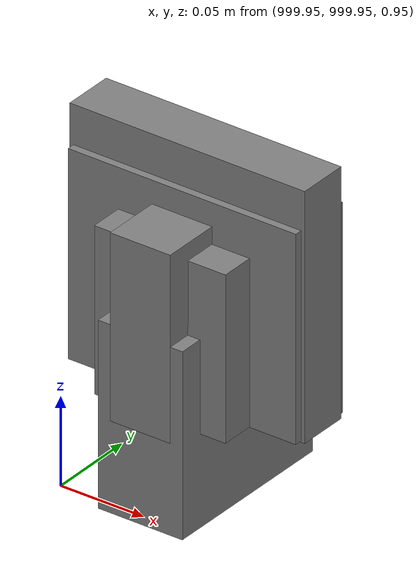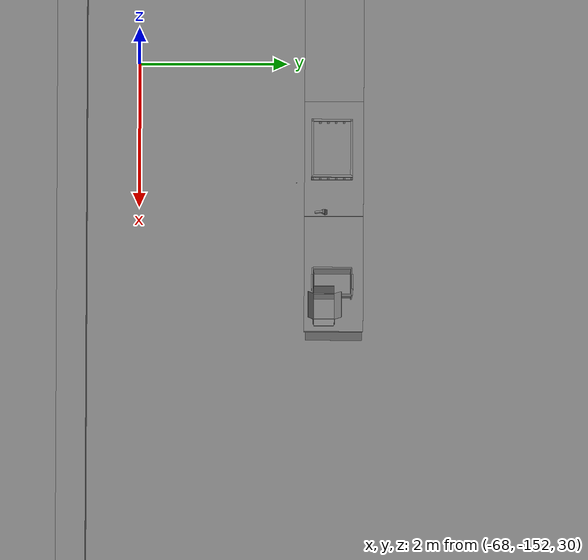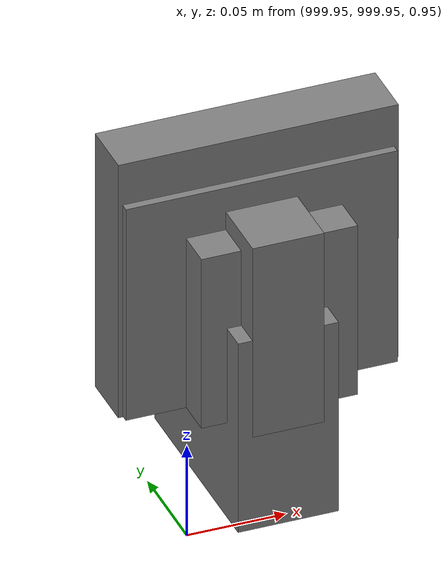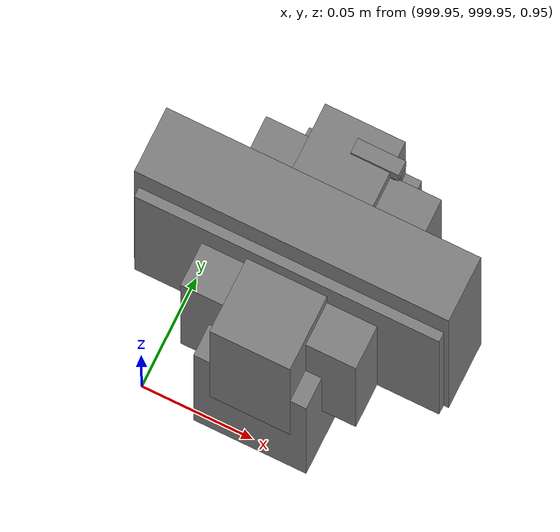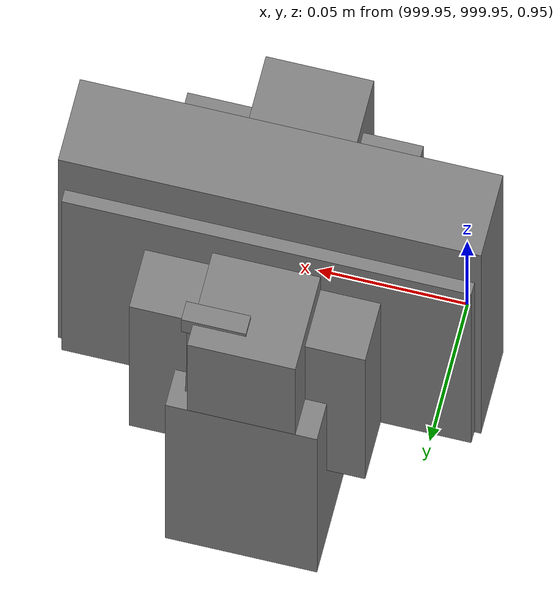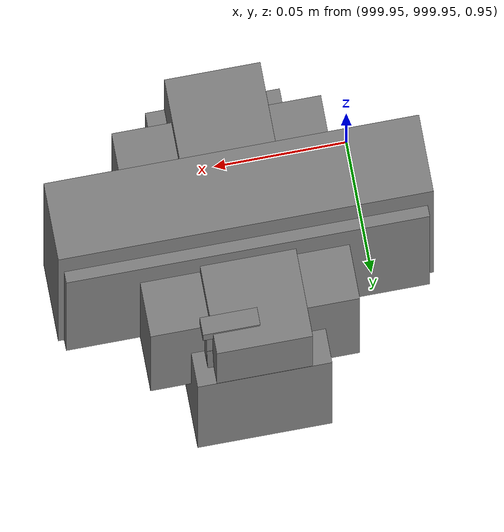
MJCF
<mujoco>
    <option gravity="0.000000000 0.000000000 -9.810000420" timestep="0.0049999999" integrator="implicitfast" density="1.225" viscosity="1.8000001e-05" noslip_iterations="10" iterations="100" sdf_iterations="50">
        <flag multiccd="disable"/>
    </option>
    <size memory="1000M"/>
    <compiler coordinate="local"/>
    <worldbody>
        <light cutoff="30" pos="0 1 1" dir="0 -1 -2"/>
        <light cutoff="30" pos="0 -1 1" dir="0 1 -2"/>
        <body pos="-64.866622925 -149.383972168 30.183746338" euler="89.999984741 89.999946594 0.000000000" name="openloong_gripper_2f85_fix_base_usda_bluebox_01">
            <geom contype="1" conaffinity="1" density="1000" type="box" material="" rgba="0.500000000 0.500000000 0.500000000 1.000000000" solimp="0.899999976 0.949999988 0.001000000" friction="1.000000000 0.005000000 0.000100000" solref="0.020000000 1.000000000" margin="0" condim="3" group="0" pos="0.276580811 0.187225342 0.000068665" quat="0.707106948 0.000077471 0.707106352 0.000077486" size="0.100000001 0.057999998 0.010000000" name="openloong_gripper_2f85_fix_base_usda_geom_65537D8E_0476_49ED_9CA1_4AA1E4C6B8DD"/>
            <geom contype="1" conaffinity="1" density="1000" type="box" material="" rgba="0.500000000 0.500000000 0.500000000 1.000000000" solimp="0.899999976 0.949999988 0.001000000" friction="1.000000000 0.005000000 0.000100000" solref="0.020000000 1.000000000" margin="0" condim="3" group="0" pos="0.000000000 0.002883911 0.000000000" quat="0.999999881 0.000000000 0.000000000 0.000000000" size="0.254000008 0.003000000 0.172000006" name="openloong_gripper_2f85_fix_base_usda_geom_3439B50D_9839_4AD5_9923_5DE383DD2F69"/>
            <geom contype="1" conaffinity="1" density="1000" type="box" material="" rgba="0.500000000 0.500000000 0.500000000 1.000000000" solimp="0.899999976 0.949999988 0.001000000" friction="1.000000000 0.005000000 0.000100000" solref="0.020000000 1.000000000" margin="0" condim="3" group="0" pos="0.000000000 0.124874115 0.173484802" quat="0.999796331 0.020176515 -0.000000015 0.000000030" size="0.259999990 0.119999997 0.007000000" name="openloong_gripper_2f85_fix_base_usda_geom_3CAB913B_AF02_49F1_A3E7_97EEEF5901B8"/>
            <geom contype="1" conaffinity="1" density="1000" type="box" material="" rgba="0.500000000 0.500000000 0.500000000 1.000000000" solimp="0.899999976 0.949999988 0.001000000" friction="1.000000000 0.005000000 0.000100000" solref="0.020000000 1.000000000" margin="0" condim="3" group="0" pos="0.000000000 0.124874115 -0.173469543" quat="0.999796331 -0.020176545 -0.000000015 0.000000000" size="0.259999990 0.119999997 0.007000000" name="openloong_gripper_2f85_fix_base_usda_geom_08545ED9_4541_4B1B_A82F_F929007C345F"/>
            <geom contype="1" conaffinity="1" density="1000" type="box" material="" rgba="0.500000000 0.500000000 0.500000000 1.000000000" solimp="0.899999976 0.949999988 0.001000000" friction="1.000000000 0.005000000 0.000100000" solref="0.020000000 1.000000000" margin="0" condim="3" group="0" pos="0.000000000 0.214008331 0.188980103" quat="0.999912977 0.013176724 0.000000015 0.000000000" size="0.259999990 0.029999999 0.012500000" name="openloong_gripper_2f85_fix_base_usda_geom_33858106_D5B7_442F_BCD6_BDAFB717AD0A"/>
            <geom contype="1" conaffinity="1" density="1000" type="box" material="" rgba="0.500000000 0.500000000 0.500000000 1.000000000" solimp="0.899999976 0.949999988 0.001000000" friction="1.000000000 0.005000000 0.000100000" solref="0.020000000 1.000000000" margin="0" condim="3" group="0" pos="-0.258361816 0.125289917 0.001876831" quat="0.702796936 -0.020792112 0.710783124 0.020769298" size="0.189999998 0.119999997 0.009000000" name="openloong_gripper_2f85_fix_base_usda_geom_E0D9D941_E8D3_4F0B_B4A2_EB00384687B0"/>
            <geom contype="1" conaffinity="1" density="1000" type="box" material="" rgba="0.500000000 0.500000000 0.500000000 1.000000000" solimp="0.899999976 0.949999988 0.001000000" friction="1.000000000 0.005000000 0.000100000" solref="0.020000000 1.000000000" margin="0" condim="3" group="0" pos="0.000000000 0.214008331 -0.188980103" quat="0.999912977 -0.013176769 0.000000030 0.000000015" size="0.259999990 0.029999999 0.012500000" name="openloong_gripper_2f85_fix_base_usda_geom_F08BE5D2_EB3E_4111_A58A_1B435AA7BD81"/>
            <geom contype="1" conaffinity="1" density="1000" type="box" material="" rgba="0.500000000 0.500000000 0.500000000 1.000000000" solimp="0.899999976 0.949999988 0.001000000" friction="1.000000000 0.005000000 0.000100000" solref="0.020000000 1.000000000" margin="0" condim="3" group="0" pos="-0.276611328 0.187225342 0.000068665" quat="0.707106650 0.000077441 0.707106709 0.000077456" size="0.100000001 0.057999998 0.010000000" name="openloong_gripper_2f85_fix_base_usda_geom_010750B7_4474_411C_A812_2952CD75C579"/>
            <geom contype="1" conaffinity="1" density="1000" type="box" material="" rgba="0.500000000 0.500000000 0.500000000 1.000000000" solimp="0.899999976 0.949999988 0.001000000" friction="1.000000000 0.005000000 0.000100000" solref="0.020000000 1.000000000" margin="0" condim="3" group="0" pos="0.258331299 0.125289917 0.001876831" quat="0.702851415 0.018856421 0.710823774 -0.019329369" size="0.189999998 0.119999997 0.009000000" name="openloong_gripper_2f85_fix_base_usda_geom_7CE5FEF9_FB90_4160_A500_192153775505"/>
            <freejoint name="openloong_gripper_2f85_fix_base_usda_bluebox_01_joint"/>
            <site size="0.005000000 0.005000000 0.005000000" rgba="0.500000000 0.500000000 0.500000000 1.000000000" pos="0.000000000 0.000000000 0.000000000" quat="0.999961913 0.008726534 0.000000000 0.000000000" group="0" type="sphere" name="openloong_gripper_2f85_fix_base_usda_bluebox_01site"/>
        </body>
        <body pos="-64.496299744 -149.491867065 30.235729218" euler="0.000000000 0.000000000 89.999946594" name="openloong_gripper_2f85_fix_base_usda_cardboardbox_01">
            <geom contype="1" conaffinity="1" density="1000" type="box" material="" rgba="0.500000000 0.500000000 0.500000000 1.000000000" solimp="0.899999976 0.949999988 0.001000000" friction="1.000000000 0.005000000 0.000100000" solref="0.020000000 1.000000000" margin="0" condim="3" group="0" pos="-0.003166199 -0.004086494 0.005052090" quat="1.000000000 0.000000000 0.000000000 0.000000000" size="0.142499998 0.177500010 0.005000000" name="openloong_gripper_2f85_fix_base_usda_geom_3FB3F078_BD42_40E8_B2C6_5A54D3CD33A7"/>
            <geom contype="1" conaffinity="1" density="1000" type="box" material="" rgba="0.500000000 0.500000000 0.500000000 1.000000000" solimp="0.899999976 0.949999988 0.001000000" friction="1.000000000 0.005000000 0.000100000" solref="0.020000000 1.000000000" margin="0" condim="3" group="0" pos="-0.003166199 0.170316696 0.150570869" quat="1.000000000 0.000000000 0.000000000 0.000000000" size="0.142499998 0.005000000 0.149999991" name="openloong_gripper_2f85_fix_base_usda_geom_407C4EEA_7C91_4678_AF47_6A8347D6D32E"/>
            <geom contype="1" conaffinity="1" density="1000" type="box" material="" rgba="0.500000000 0.500000000 0.500000000 1.000000000" solimp="0.899999976 0.949999988 0.001000000" friction="1.000000000 0.005000000 0.000100000" solref="0.020000000 1.000000000" margin="0" condim="3" group="0" pos="-0.147399902 -0.005307198 0.150570869" quat="1.000000000 0.000000000 0.000000000 0.000000000" size="0.005000000 0.177500010 0.149999991" name="openloong_gripper_2f85_fix_base_usda_geom_B3A10B3E_A84D_4379_916E_0F12AEC26AA9"/>
            <geom contype="1" conaffinity="1" density="1000" type="box" material="" rgba="0.500000000 0.500000000 0.500000000 1.000000000" solimp="0.899999976 0.949999988 0.001000000" friction="1.000000000 0.005000000 0.000100000" solref="0.020000000 1.000000000" margin="0" condim="3" group="0" pos="0.140275955 -0.005307198 0.150570869" quat="1.000000000 0.000000000 0.000000000 0.000000000" size="0.005000000 0.177500010 0.149999991" name="openloong_gripper_2f85_fix_base_usda_geom_A0385ABF_C96D_41BF_944E_F9CDC63F06B2"/>
            <geom contype="1" conaffinity="1" density="1000" type="box" material="" rgba="0.500000000 0.500000000 0.500000000 1.000000000" solimp="0.899999976 0.949999988 0.001000000" friction="1.000000000 0.005000000 0.000100000" solref="0.020000000 1.000000000" margin="0" condim="3" group="0" pos="-0.003166199 -0.181550980 0.150570869" quat="1.000000000 0.000000000 0.000000000 0.000000000" size="0.142499998 0.005000000 0.149999991" name="openloong_gripper_2f85_fix_base_usda_geom_65905863_E73E_4B16_BE67_68319DCF69EA"/>
            <freejoint name="openloong_gripper_2f85_fix_base_usda_cardboardbox_01_joint"/>
            <site size="0.005000000 0.005000000 0.005000000" rgba="0.500000000 0.500000000 0.500000000 1.000000000" pos="0.000000000 0.000000000 0.000000000" quat="0.999961913 0.008726535 0.000000000 0.000000000" group="0" type="sphere" name="openloong_gripper_2f85_fix_base_usda_site_5AF90EE6_E054_4B94_9A87_2D5F8835972E"/>
            <body pos="0.139160156 -0.004048347 0.301930904" euler="-179.999954224 49.383502960 179.999954224" name="openloong_gripper_2f85_fix_base_usda_A1_006">
                <geom contype="1" conaffinity="1" density="1000" type="box" material="" rgba="0.500000000 0.500000000 0.500000000 1.000000000" solimp="0.899999976 0.949999988 0.001000000" friction="1.000000000 0.005000000 0.000100000" solref="0.020000000 1.000000000" margin="0" condim="3" group="0" pos="-0.071587563 0.000009537 0.001745224" quat="0.999999881 0.000000000 0.000000000 0.000000000" size="0.071249999 0.179999992 0.002500000" name="openloong_gripper_2f85_fix_base_usda_geom_52BB75D2_51BC_4118_9FA6_DD9D79B4651D"/>
                <joint armature="0" stiffness="0.07" damping="0.0099999998" axis="0.000000 1.000000 0.000000" type="hinge" name="openloong_gripper_2f85_fix_base_usda_A1_006"/>
            </body>
            <body pos="-0.145902634 -0.004086494 0.301938057" euler="-180.000000000 -60.000011444 -180.000000000" name="openloong_gripper_2f85_fix_base_usda_A2_006">
                <geom contype="1" conaffinity="1" density="1000" type="box" material="" rgba="0.500000000 0.500000000 0.500000000 1.000000000" solimp="0.899999976 0.949999988 0.001000000" friction="1.000000000 0.005000000 0.000100000" solref="0.020000000 1.000000000" margin="0" condim="3" group="0" pos="0.071268082 0.000009537 0.002717972" quat="0.000002921 0.000000000 -0.000000030 0.999999881" size="0.071249999 0.179999992 0.002500000" name="openloong_gripper_2f85_fix_base_usda_geom_8786FCD0_0CDA_4AC2_B148_95936A327A6B"/>
                <joint armature="0" stiffness="0.07" damping="0.0099999998" axis="0.000000 1.000000 0.000000" type="hinge" name="openloong_gripper_2f85_fix_base_usda_A2_006"/>
            </body>
            <body pos="-0.003385544 0.175991058 0.301930904" euler="-125.858116150 -0.000004561 0.000002331" name="openloong_gripper_2f85_fix_base_usda_B2_006">
                <geom contype="1" conaffinity="1" density="1000" type="box" material="" rgba="0.500000000 0.500000000 0.500000000 1.000000000" solimp="0.899999976 0.949999988 0.001000000" friction="1.000000000 0.005000000 0.000100000" solref="0.020000000 1.000000000" margin="0" condim="3" group="0" pos="0.000009537 -0.070939064 -0.002470016" quat="0.999614120 0.027776197 -0.000000015 0.000000030" size="0.137500003 0.064999998 0.005000000" name="openloong_gripper_2f85_fix_base_usda_geom_3C15E79F_29BC_4762_8E50_01CF5671E2A5"/>
                <joint armature="0" stiffness="0.07" damping="0.0099999998" axis="1.000000 0.000000 0.000000" type="hinge" name="openloong_gripper_2f85_fix_base_usda_B2_006"/>
            </body>
            <body pos="-0.003385544 -0.184140205 0.301938057" euler="147.805557251 0.000000000 0.000000000" name="openloong_gripper_2f85_fix_base_usda_B1_006">
                <geom contype="1" conaffinity="1" density="1000" type="box" material="" rgba="0.500000000 0.500000000 0.500000000 1.000000000" solimp="0.899999976 0.949999988 0.001000000" friction="1.000000000 0.005000000 0.000100000" solref="0.020000000 1.000000000" margin="0" condim="3" group="0" pos="-0.000028610 0.070202351 -0.002703667" quat="0.999614179 -0.027776167 0.000000000 0.000000000" size="0.137500003 0.064999998 0.005000000" name="openloong_gripper_2f85_fix_base_usda_geom_C5DB9DC1_E13A_4044_9680_42204235B08E"/>
                <joint armature="0" stiffness="0.07" damping="0.0099999998" axis="1.000000 0.000000 0.000000" type="hinge" name="openloong_gripper_2f85_fix_base_usda_B1_006"/>
            </body>
        </body>
        <body pos="-65.882858276 -149.481979370 30.229999542" euler="-64.487716675 0.000000000 0.000000000" name="openloong_gripper_2f85_fix_base_usda_Barcode">
            <geom contype="1" conaffinity="1" density="1000" type="box" material="" rgba="0.500000000 0.500000000 0.500000000 1.000000000" solimp="0.899999976 0.949999988 0.001000000" friction="1.000000000 0.005000000 0.000100000" solref="0.020000000 1.000000000" margin="0" condim="3" group="0" pos="0.000000000 0.013038635 0.001419067" quat="0.000000000 0.000000000 0.000000000 1.000000119" size="0.034000002 0.010000000 0.017999999" name="openloong_gripper_2f85_fix_base_usda_geom_07B10BE1_2CD9_456B_8DDC_4C3370BF77EF"/>
            <geom contype="1" conaffinity="1" density="1000" type="box" material="" rgba="0.500000000 0.500000000 0.500000000 1.000000000" solimp="0.899999976 0.949999988 0.001000000" friction="1.000000000 0.005000000 0.000100000" solref="0.020000000 1.000000000" margin="0" condim="3" group="0" pos="0.000000000 -0.035301208 -0.007095337" quat="0.000000000 0.000000000 -0.043619365 0.999048233" size="0.028999999 0.010000000 0.020000000" name="openloong_gripper_2f85_fix_base_usda_geom_9804FDA9_3C45_4268_B9EB_566F75069ACE"/>
            <geom contype="1" conaffinity="1" density="1000" type="box" material="" rgba="0.500000000 0.500000000 0.500000000 1.000000000" solimp="0.899999976 0.949999988 0.001000000" friction="1.000000000 0.005000000 0.000100000" solref="0.020000000 1.000000000" margin="0" condim="3" group="0" pos="0.000000000 -0.043411255 -0.011749268" quat="0.922262907 0.386563420 0.000000000 0.000000000" size="0.026000001 0.010000000 0.020000000" name="openloong_gripper_2f85_fix_base_usda_geom_4C4917BD_54ED_4CC1_8AF3_DFFD5E1DCA1F"/>
            <geom contype="1" conaffinity="1" density="1000" type="box" material="" rgba="0.500000000 0.500000000 0.500000000 1.000000000" solimp="0.899999976 0.949999988 0.001000000" friction="1.000000000 0.005000000 0.000100000" solref="0.020000000 1.000000000" margin="0" condim="3" group="0" pos="0.000000000 -0.016967773 -0.031860352" quat="0.000000000 0.000000000 0.000000000 1.000000119" size="0.008000000 0.010000000 0.013000000" name="openloong_gripper_2f85_fix_base_usda_geom_12D20D5D_17C4_4F1B_B5D3_B9F9C1D4A51D"/>
            <geom contype="1" conaffinity="1" density="1000" type="box" material="" rgba="0.500000000 0.500000000 0.500000000 1.000000000" solimp="0.899999976 0.949999988 0.001000000" friction="1.000000000 0.005000000 0.000100000" solref="0.020000000 1.000000000" margin="0" condim="3" group="0" pos="0.000000000 -0.001869202 0.000312805" quat="0.953716993 0.300705761 0.000000000 0.000000000" size="0.032000002 0.010000000 0.018999999" name="openloong_gripper_2f85_fix_base_usda_geom_7AB3DE00_A4AF_444B_9FA4_96173602EF39"/>
            <geom contype="1" conaffinity="1" density="1000" type="box" material="" rgba="0.500000000 0.500000000 0.500000000 1.000000000" solimp="0.899999976 0.949999988 0.001000000" friction="1.000000000 0.005000000 0.000100000" solref="0.020000000 1.000000000" margin="0" condim="3" group="0" pos="0.000000000 -0.019531250 -0.003173828" quat="0.953716993 0.300705761 0.000000000 0.000000000" size="0.030999999 0.010000000 0.020000000" name="openloong_gripper_2f85_fix_base_usda_geom_BC346039_5DEF_44FB_BA8F_9EF4C32CA145"/>
            <geom contype="1" conaffinity="1" density="1000" type="box" material="" rgba="0.500000000 0.500000000 0.500000000 1.000000000" solimp="0.899999976 0.949999988 0.001000000" friction="1.000000000 0.005000000 0.000100000" solref="0.020000000 1.000000000" margin="0" condim="3" group="0" pos="0.000000000 -0.035301208 -0.007095337" quat="0.953716993 0.300705761 0.000000000 0.000000000" size="0.028999999 0.010000000 0.020000000" name="openloong_gripper_2f85_fix_base_usda_geom_93E15C7D_355A_4CB9_8DF3_798B83B5395F"/>
            <geom contype="1" conaffinity="1" density="1000" type="box" material="" rgba="0.500000000 0.500000000 0.500000000 1.000000000" solimp="0.899999976 0.949999988 0.001000000" friction="1.000000000 0.005000000 0.000100000" solref="0.020000000 1.000000000" margin="0" condim="3" group="0" pos="0.000000000 -0.042617798 -0.071121216" quat="0.000000000 0.000000000 0.000000000 1.000000119" size="0.013000000 0.021000000 0.059999999" name="openloong_gripper_2f85_fix_base_usda_geom_3AE47695_09B0_4F71_BF83_2F51961B5B79"/>
            <freejoint name="openloong_gripper_2f85_fix_base_usda_Barcode_joint"/>
            <site size="0.005000000 0.005000000 0.005000000" rgba="0.500000000 0.500000000 0.500000000 1.000000000" pos="0.000000000 0.000000000 0.000000000" quat="1.000000000 0.000000000 0.000000000 0.000000000" group="0" type="sphere" name="openloong_gripper_2f85_fix_base_usda_Barcode_site"/>
        </body>
        <body pos="-66.745018005 -149.392349243 30.184000015" euler="0.000000000 0.000000000 89.999946594" name="[22331750555180]_Basket_01">
            <geom contype="1" conaffinity="1" density="1000" type="box" material="" rgba="0.500000000 0.500000000 0.500000000 1.000000000" solimp="0.899999976 0.949999988 0.001000000" friction="1.000000000 0.005000000 0.000100000" solref="0.020000000 1.000000000" margin="0" condim="3" group="0" pos="-0.052425385 0.389207840 0.089787483" quat="0.707107008 0.000000000 0.000000000 0.707106411" size="0.014249999 0.014249999 0.059999999" name="[22331750555180]_geom_C4CF6159_E5B8_4D51_9F84_61793DB79088"/>
            <geom contype="1" conaffinity="1" density="1000" type="box" material="" rgba="0.500000000 0.500000000 0.500000000 1.000000000" solimp="0.899999976 0.949999988 0.001000000" friction="1.000000000 0.005000000 0.000100000" solref="0.020000000 1.000000000" margin="0" condim="3" group="0" pos="0.264015198 -0.133043289 0.089787483" quat="0.707107008 0.000000000 0.000000000 0.707106411" size="0.014249999 0.014249999 0.059999999" name="[22331750555180]_geom_3024613F_FAE7_478A_B665_B37033D4DB80"/>
            <geom contype="1" conaffinity="1" density="1000" type="box" material="" rgba="0.500000000 0.500000000 0.500000000 1.000000000" solimp="0.899999976 0.949999988 0.001000000" friction="1.000000000 0.005000000 0.000100000" solref="0.020000000 1.000000000" margin="0" condim="3" group="0" pos="-0.264015198 -0.265548706 0.089793205" quat="0.707107008 0.000000000 0.000000000 0.707106411" size="0.014249999 0.014249999 0.059999999" name="[22331750555180]_geom_FE775E68_B279_4F5A_B4AE_A9610B36EF50"/>
            <geom contype="1" conaffinity="1" density="1000" type="box" material="" rgba="0.500000000 0.500000000 0.500000000 1.000000000" solimp="0.899999976 0.949999988 0.001000000" friction="1.000000000 0.005000000 0.000100000" solref="0.020000000 1.000000000" margin="0" condim="3" group="0" pos="-0.160263062 -0.389322281 0.089793205" quat="0.707107008 0.000000000 0.000000000 0.707106411" size="0.014249999 0.014249999 0.059999999" name="[22331750555180]_geom_FE42D0F3_187B_4E32_A4B3_22E88EA2AA77"/>
            <geom contype="1" conaffinity="1" density="1000" type="box" material="" rgba="0.500000000 0.500000000 0.500000000 1.000000000" solimp="0.899999976 0.949999988 0.001000000" friction="1.000000000 0.005000000 0.000100000" solref="0.020000000 1.000000000" margin="0" condim="3" group="0" pos="0.162265778 -0.389322281 0.089787483" quat="0.707107008 0.000000000 0.000000000 0.707106411" size="0.014249999 0.014249999 0.059999999" name="[22331750555180]_geom_1C89A3E1_1CD2_473A_B978_FC648B4BB5FF"/>
            <geom contype="1" conaffinity="1" density="1000" type="box" material="" rgba="0.500000000 0.500000000 0.500000000 1.000000000" solimp="0.899999976 0.949999988 0.001000000" friction="1.000000000 0.005000000 0.000100000" solref="0.020000000 1.000000000" margin="0" condim="3" group="0" pos="0.264015198 0.389207840 0.089787483" quat="0.707107008 0.000000000 0.000000000 0.707106411" size="0.014249999 0.014249999 0.059999999" name="[22331750555180]_geom_91501817_5E9D_45FA_861A_D88127DB602B"/>
            <geom contype="1" conaffinity="1" density="1000" type="box" material="" rgba="0.500000000 0.500000000 0.500000000 1.000000000" solimp="0.899999976 0.949999988 0.001000000" friction="1.000000000 0.005000000 0.000100000" solref="0.020000000 1.000000000" margin="0" condim="3" group="0" pos="-0.264015198 -0.133043289 0.089793205" quat="0.707107008 0.000000000 0.000000000 0.707106411" size="0.014249999 0.014249999 0.059999999" name="[22331750555180]_geom_DBF85C59_480E_4B94_9A63_27E970AFB248"/>
            <geom contype="1" conaffinity="1" density="1000" type="box" material="" rgba="0.500000000 0.500000000 0.500000000 1.000000000" solimp="0.899999976 0.949999988 0.001000000" friction="1.000000000 0.005000000 0.000100000" solref="0.020000000 1.000000000" margin="0" condim="3" group="0" pos="-0.264026642 0.269256592 0.089793205" quat="0.707107008 0.000000000 0.000000000 0.707106411" size="0.014249999 0.014249999 0.059999999" name="[22331750555180]_geom_9C1A9442_C5A5_47C7_8710_576F8B322D94"/>
            <geom contype="1" conaffinity="1" density="1000" type="box" material="" rgba="0.500000000 0.500000000 0.500000000 1.000000000" solimp="0.899999976 0.949999988 0.001000000" friction="1.000000000 0.005000000 0.000100000" solref="0.020000000 1.000000000" margin="0" condim="3" group="0" pos="0.054462433 0.389207840 0.089787483" quat="0.707107008 0.000000000 0.000000000 0.707106411" size="0.014249999 0.014249999 0.059999999" name="[22331750555180]_geom_CE30C548_5D25_41B4_8EC7_B770A4B44F4F"/>
            <geom contype="1" conaffinity="1" density="1000" type="box" material="" rgba="0.500000000 0.500000000 0.500000000 1.000000000" solimp="0.899999976 0.949999988 0.001000000" friction="1.000000000 0.005000000 0.000100000" solref="0.020000000 1.000000000" margin="0" condim="3" group="0" pos="0.054462433 -0.389322281 0.089787483" quat="0.707107008 0.000000000 0.000000000 0.707106411" size="0.014249999 0.014249999 0.059999999" name="[22331750555180]_geom_6EF21A0D_8218_4E12_8A1C_5D59C89FDBFE"/>
            <geom contype="1" conaffinity="1" density="1000" type="box" material="" rgba="0.500000000 0.500000000 0.500000000 1.000000000" solimp="0.899999976 0.949999988 0.001000000" friction="1.000000000 0.005000000 0.000100000" solref="0.020000000 1.000000000" margin="0" condim="3" group="0" pos="0.264015198 0.269256592 0.089793205" quat="0.707107008 0.000000000 0.000000000 0.707106411" size="0.014249999 0.014249999 0.059999999" name="[22331750555180]_geom_361B717D_AED6_4BDF_BF5A_03E79FC86414"/>
            <geom contype="1" conaffinity="1" density="1000" type="box" material="" rgba="0.500000000 0.500000000 0.500000000 1.000000000" solimp="0.899999976 0.949999988 0.001000000" friction="1.000000000 0.005000000 0.000100000" solref="0.020000000 1.000000000" margin="0" condim="3" group="0" pos="0.264015198 -0.389322281 0.089787483" quat="0.707107008 0.000000000 0.000000000 0.707106411" size="0.014249999 0.014249999 0.059999999" name="[22331750555180]_geom_7B114974_8784_4CA0_A12A_5D0AE262DD53"/>
            <geom contype="1" conaffinity="1" density="1000" type="box" material="" rgba="0.500000000 0.500000000 0.500000000 1.000000000" solimp="0.899999976 0.949999988 0.001000000" friction="1.000000000 0.005000000 0.000100000" solref="0.020000000 1.000000000" margin="0" condim="3" group="0" pos="0.000000000 0.000000000 0.015998840" quat="0.707107008 0.000000000 0.000000000 0.707106411" size="0.403499991 0.279000014 0.015750000" name="[22331750555180]_geom_9D883A18_60AB_4248_B918_9CC108934050"/>
            <geom contype="1" conaffinity="1" density="1000" type="box" material="" rgba="0.500000000 0.500000000 0.500000000 1.000000000" solimp="0.899999976 0.949999988 0.001000000" friction="1.000000000 0.005000000 0.000100000" solref="0.020000000 1.000000000" margin="0" condim="3" group="0" pos="0.000000000 -0.389476776 0.163619041" quat="0.707107008 0.000000000 0.000000000 0.707106411" size="0.015000000 0.277500004 0.015750000" name="[22331750555180]_geom_AAA37A8F_7343_4D5A_99E1_30FFBDC40035"/>
            <geom contype="1" conaffinity="1" density="1000" type="box" material="" rgba="0.500000000 0.500000000 0.500000000 1.000000000" solimp="0.899999976 0.949999988 0.001000000" friction="1.000000000 0.005000000 0.000100000" solref="0.020000000 1.000000000" margin="0" condim="3" group="0" pos="0.162265778 0.389207840 0.089787483" quat="0.707107008 0.000000000 0.000000000 0.707106411" size="0.014249999 0.014249999 0.059999999" name="[22331750555180]_geom_7017F34E_A689_4D61_AC36_7162E67401F5"/>
            <geom contype="1" conaffinity="1" density="1000" type="box" material="" rgba="0.500000000 0.500000000 0.500000000 1.000000000" solimp="0.899999976 0.949999988 0.001000000" friction="1.000000000 0.005000000 0.000100000" solref="0.020000000 1.000000000" margin="0" condim="3" group="0" pos="0.000000000 0.389471054 0.163619041" quat="0.707107008 0.000000000 0.000000000 0.707106411" size="0.015000000 0.277500004 0.015750000" name="[22331750555180]_geom_FDEF563A_D88F_476C_BA6A_392D51F096AB"/>
            <geom contype="1" conaffinity="1" density="1000" type="box" material="" rgba="0.500000000 0.500000000 0.500000000 1.000000000" solimp="0.899999976 0.949999988 0.001000000" friction="1.000000000 0.005000000 0.000100000" solref="0.020000000 1.000000000" margin="0" condim="3" group="0" pos="-0.263511658 0.000000000 0.163619041" quat="0.707107008 0.000000000 0.000000000 0.707106411" size="0.403499991 0.015000000 0.015750000" name="[22331750555180]_geom_1140E328_6DF3_47FA_8F84_81F3329EAC7C"/>
            <geom contype="1" conaffinity="1" density="1000" type="box" material="" rgba="0.500000000 0.500000000 0.500000000 1.000000000" solimp="0.899999976 0.949999988 0.001000000" friction="1.000000000 0.005000000 0.000100000" solref="0.020000000 1.000000000" margin="0" condim="3" group="0" pos="-0.264015198 0.141334534 0.089793205" quat="0.707107008 0.000000000 0.000000000 0.707106411" size="0.014249999 0.014249999 0.059999999" name="[22331750555180]_geom_D37D908A_A94B_4E9E_B47A_22BE8164D8CC"/>
            <geom contype="1" conaffinity="1" density="1000" type="box" material="" rgba="0.500000000 0.500000000 0.500000000 1.000000000" solimp="0.899999976 0.949999988 0.001000000" friction="1.000000000 0.005000000 0.000100000" solref="0.020000000 1.000000000" margin="0" condim="3" group="0" pos="0.264015198 -0.265548706 0.089787483" quat="0.707107008 0.000000000 0.000000000 0.707106411" size="0.014249999 0.014249999 0.059999999" name="[22331750555180]_geom_6C82388C_F842_4BB4_ABC1_779E38376519"/>
            <geom contype="1" conaffinity="1" density="1000" type="box" material="" rgba="0.500000000 0.500000000 0.500000000 1.000000000" solimp="0.899999976 0.949999988 0.001000000" friction="1.000000000 0.005000000 0.000100000" solref="0.020000000 1.000000000" margin="0" condim="3" group="0" pos="-0.160263062 0.389207840 0.089787483" quat="0.707107008 0.000000000 0.000000000 0.707106411" size="0.014249999 0.014249999 0.059999999" name="[22331750555180]_geom_AD77E9A3_681B_413E_81B3_CEFF2D5B8AFF"/>
            <geom contype="1" conaffinity="1" density="1000" type="box" material="" rgba="0.500000000 0.500000000 0.500000000 1.000000000" solimp="0.899999976 0.949999988 0.001000000" friction="1.000000000 0.005000000 0.000100000" solref="0.020000000 1.000000000" margin="0" condim="3" group="0" pos="-0.052425385 -0.389322281 0.089787483" quat="0.707107008 0.000000000 0.000000000 0.707106411" size="0.014249999 0.014249999 0.059999999" name="[22331750555180]_geom_ECE1BF24_2105_4C5B_A33F_758083DD8202"/>
            <geom contype="1" conaffinity="1" density="1000" type="box" material="" rgba="0.500000000 0.500000000 0.500000000 1.000000000" solimp="0.899999976 0.949999988 0.001000000" friction="1.000000000 0.005000000 0.000100000" solref="0.020000000 1.000000000" margin="0" condim="3" group="0" pos="-0.264026642 -0.389322281 0.089793205" quat="0.707107008 0.000000000 0.000000000 0.707106411" size="0.014249999 0.014249999 0.059999999" name="[22331750555180]_geom_553D9680_C980_44B2_A373_C3AB270D280E"/>
            <geom contype="1" conaffinity="1" density="1000" type="box" material="" rgba="0.500000000 0.500000000 0.500000000 1.000000000" solimp="0.899999976 0.949999988 0.001000000" friction="1.000000000 0.005000000 0.000100000" solref="0.020000000 1.000000000" margin="0" condim="3" group="0" pos="0.264015198 0.141334534 0.089787483" quat="0.707107008 0.000000000 0.000000000 0.707106411" size="0.014249999 0.014249999 0.059999999" name="[22331750555180]_geom_6C40EF70_5D47_49C0_BD37_0E68188B8786"/>
            <geom contype="1" conaffinity="1" density="1000" type="box" material="" rgba="0.500000000 0.500000000 0.500000000 1.000000000" solimp="0.899999976 0.949999988 0.001000000" friction="1.000000000 0.005000000 0.000100000" solref="0.020000000 1.000000000" margin="0" condim="3" group="0" pos="-0.264015198 0.389207840 0.089793205" quat="0.707107008 0.000000000 0.000000000 0.707106411" size="0.014249999 0.014249999 0.059999999" name="[22331750555180]_geom_FB92FA56_041C_4AA7_A302_8F61A4C132DD"/>
            <geom contype="1" conaffinity="1" density="1000" type="box" material="" rgba="0.500000000 0.500000000 0.500000000 1.000000000" solimp="0.899999976 0.949999988 0.001000000" friction="1.000000000 0.005000000 0.000100000" solref="0.020000000 1.000000000" margin="0" condim="3" group="0" pos="0.264015198 0.004480362 0.089787483" quat="0.707107008 0.000000000 0.000000000 0.707106411" size="0.014249999 0.014249999 0.059999999" name="[22331750555180]_geom_25E67F7B_F805_474B_BBAC_FFC18171AD69"/>
            <geom contype="1" conaffinity="1" density="1000" type="box" material="" rgba="0.500000000 0.500000000 0.500000000 1.000000000" solimp="0.899999976 0.949999988 0.001000000" friction="1.000000000 0.005000000 0.000100000" solref="0.020000000 1.000000000" margin="0" condim="3" group="0" pos="0.263694763 -0.000011444 0.163619041" quat="0.707107008 0.000000000 0.000000000 0.707106411" size="0.403499991 0.015000000 0.015750000" name="[22331750555180]_geom_664E2EAF_1F92_452E_A5C9_9F53C7DD61AB"/>
            <geom contype="1" conaffinity="1" density="1000" type="box" material="" rgba="0.500000000 0.500000000 0.500000000 1.000000000" solimp="0.899999976 0.949999988 0.001000000" friction="1.000000000 0.005000000 0.000100000" solref="0.020000000 1.000000000" margin="0" condim="3" group="0" pos="-0.264015198 0.004480362 0.089793205" quat="0.707107008 0.000000000 0.000000000 0.707106411" size="0.014249999 0.014249999 0.059999999" name="[22331750555180]_geom_D8E13576_3897_4537_B1C1_588FBF8003C0"/>
            <freejoint name="[22331750555180]_joint_33AE2D57_C6CB_4B6B_8470_CB3CEBD28A4D"/>
        </body>
        <body pos="0.000000000 0.000000000 0.000000000" euler="0.000000000 0.000000000 0.000000000" name="Static Objects_Static Objects">
            <geom contype="1" conaffinity="1" density="1000" type="box" material="" rgba="0.500000000 0.500000000 0.500000000 1.000000000" solimp="0.899999976 0.949999988 0.001000000" friction="1.000000000 0.005000000 0.000100000" solref="0.020000000 1.000000000" margin="0" condim="3" group="0" pos="-67.544113159 -149.365814209 29.727830887" quat="0.500000417 0.499999970 0.499999553 0.499999970" size="0.381000012 0.319999993 0.041000001" name="Static Objects_geom_92691197_2F6B_4795_AF97_C4F5B900D8EA"/>
            <geom contype="1" conaffinity="1" density="1000" type="box" material="" rgba="0.500000000 0.500000000 0.500000000 1.000000000" solimp="0.899999976 0.949999988 0.001000000" friction="1.000000000 0.005000000 0.000100000" solref="0.020000000 1.000000000" margin="0" condim="3" group="0" pos="-68.239501953 -149.365814209 30.086868286" quat="0.500000417 0.499999970 0.499999553 0.499999970" size="0.370999992 0.039500002 0.745000005" name="Static Objects_geom_DC2234F0_827E_424E_AC5E_8CA0D0E13290"/>
            <geom contype="1" conaffinity="1" density="1000" type="box" material="" rgba="0.500000000 0.500000000 0.500000000 1.000000000" solimp="0.899999976 0.949999988 0.001000000" friction="1.000000000 0.005000000 0.000100000" solref="0.020000000 1.000000000" margin="0" condim="3" group="0" pos="-68.239501953 -149.365814209 30.147235870" quat="0.500000417 0.499999970 0.499999553 0.499999970" size="0.400000006 0.022000000 0.800000012" name="Static Objects_geom_3E76CAFD_A1DE_4F6F_9CAD_43B264BDA25E"/>
            <geom contype="1" conaffinity="1" density="1000" type="box" material="" rgba="0.500000000 0.500000000 0.500000000 1.000000000" solimp="0.899999976 0.949999988 0.001000000" friction="1.000000000 0.005000000 0.000100000" solref="0.020000000 1.000000000" margin="0" condim="3" group="0" pos="-68.934890747 -149.365814209 29.727830887" quat="0.500000417 0.499999970 0.499999553 0.499999970" size="0.381000012 0.319999993 0.041000001" name="Static Objects_geom_C1737411_F858_44EC_8CBD_A28049B7203D"/>
            <geom contype="1" conaffinity="1" density="1000" type="box" material="" rgba="0.500000000 0.500000000 0.500000000 1.000000000" solimp="0.899999976 0.949999988 0.001000000" friction="1.000000000 0.005000000 0.000100000" solref="0.020000000 1.000000000" margin="0" condim="3" group="0" pos="-68.239501953 -149.365814209 29.561563492" quat="0.500000417 0.499999970 0.499999553 0.499999970" size="0.020000000 0.022000000 0.660000026" name="Static Objects_geom_A50D1154_25AC_41BD_8414_9FCDD928296D"/>
            <geom contype="1" conaffinity="1" density="1000" type="box" material="" rgba="0.500000000 0.500000000 0.500000000 1.000000000" solimp="0.899999976 0.949999988 0.001000000" friction="1.000000000 0.005000000 0.000100000" solref="0.020000000 1.000000000" margin="0" condim="3" group="0" pos="-65.945671082 -149.365814209 29.727830887" quat="0.500000417 0.499999970 0.499999553 0.499999970" size="0.381000012 0.319999993 0.041000001" name="Static Objects_geom_F2330AA9_0964_4228_8344_8C49B5A0D20C"/>
            <geom contype="1" conaffinity="1" density="1000" type="box" material="" rgba="0.500000000 0.500000000 0.500000000 1.000000000" solimp="0.899999976 0.949999988 0.001000000" friction="1.000000000 0.005000000 0.000100000" solref="0.020000000 1.000000000" margin="0" condim="3" group="0" pos="-66.641059875 -149.365814209 30.086868286" quat="0.500000417 0.499999970 0.499999553 0.499999970" size="0.370999992 0.039500002 0.745000005" name="Static Objects_geom_04378662_9FC0_4D94_83C4_B175449F4C2A"/>
            <geom contype="1" conaffinity="1" density="1000" type="box" material="" rgba="0.500000000 0.500000000 0.500000000 1.000000000" solimp="0.899999976 0.949999988 0.001000000" friction="1.000000000 0.005000000 0.000100000" solref="0.020000000 1.000000000" margin="0" condim="3" group="0" pos="-66.641059875 -149.365814209 30.147235870" quat="0.500000417 0.499999970 0.499999553 0.499999970" size="0.400000006 0.022000000 0.800000012" name="Static Objects_geom_31DE1045_77F9_4B72_9440_BFEB55FAD52D"/>
            <geom contype="1" conaffinity="1" density="1000" type="box" material="" rgba="0.500000000 0.500000000 0.500000000 1.000000000" solimp="0.899999976 0.949999988 0.001000000" friction="1.000000000 0.005000000 0.000100000" solref="0.020000000 1.000000000" margin="0" condim="3" group="0" pos="-67.336448669 -149.365814209 29.727830887" quat="0.500000417 0.499999970 0.499999553 0.499999970" size="0.381000012 0.319999993 0.041000001" name="Static Objects_geom_9CFA7397_8B62_4150_BDC1_07A95AD61BF3"/>
            <geom contype="1" conaffinity="1" density="1000" type="box" material="" rgba="0.500000000 0.500000000 0.500000000 1.000000000" solimp="0.899999976 0.949999988 0.001000000" friction="1.000000000 0.005000000 0.000100000" solref="0.020000000 1.000000000" margin="0" condim="3" group="0" pos="-66.641059875 -149.365814209 29.561563492" quat="0.500000417 0.499999970 0.499999553 0.499999970" size="0.020000000 0.022000000 0.660000026" name="Static Objects_geom_EFE1C20F_056B_4BCB_B843_0D0DE6D57756"/>
            <geom contype="1" conaffinity="1" density="1000" type="box" material="" rgba="0.500000000 0.500000000 0.500000000 1.000000000" solimp="0.899999976 0.949999988 0.001000000" friction="1.000000000 0.005000000 0.000100000" solref="0.020000000 1.000000000" margin="0" condim="3" group="0" pos="-64.338577271 -149.365814209 29.727830887" quat="0.500000417 0.499999970 0.499999553 0.499999970" size="0.381000012 0.319999993 0.041000001" name="Static Objects_geom_91CB7D63_E3B6_4271_B0DF_1F110E6E2781"/>
            <geom contype="1" conaffinity="1" density="1000" type="box" material="" rgba="0.500000000 0.500000000 0.500000000 1.000000000" solimp="0.899999976 0.949999988 0.001000000" friction="1.000000000 0.005000000 0.000100000" solref="0.020000000 1.000000000" margin="0" condim="3" group="0" pos="-65.033966064 -149.365814209 30.086868286" quat="0.500000417 0.499999970 0.499999553 0.499999970" size="0.370999992 0.039500002 0.745000005" name="Static Objects_geom_49DC06E0_6F00_4875_9023_7338AE0E25D2"/>
            <geom contype="1" conaffinity="1" density="1000" type="box" material="" rgba="0.500000000 0.500000000 0.500000000 1.000000000" solimp="0.899999976 0.949999988 0.001000000" friction="1.000000000 0.005000000 0.000100000" solref="0.020000000 1.000000000" margin="0" condim="3" group="0" pos="-65.033966064 -149.365814209 30.147235870" quat="0.500000417 0.499999970 0.499999553 0.499999970" size="0.400000006 0.022000000 0.800000012" name="Static Objects_geom_F40991D0_93AC_40C4_A4D5_68BBAB43AEA7"/>
            <geom contype="1" conaffinity="1" density="1000" type="box" material="" rgba="0.500000000 0.500000000 0.500000000 1.000000000" solimp="0.899999976 0.949999988 0.001000000" friction="1.000000000 0.005000000 0.000100000" solref="0.020000000 1.000000000" margin="0" condim="3" group="0" pos="-65.729354858 -149.365814209 29.727830887" quat="0.500000417 0.499999970 0.499999553 0.499999970" size="0.381000012 0.319999993 0.041000001" name="Static Objects_geom_FF9F4E27_680E_4172_B610_97474802B0E6"/>
            <geom contype="1" conaffinity="1" density="1000" type="box" material="" rgba="0.500000000 0.500000000 0.500000000 1.000000000" solimp="0.899999976 0.949999988 0.001000000" friction="1.000000000 0.005000000 0.000100000" solref="0.020000000 1.000000000" margin="0" condim="3" group="0" pos="-65.033966064 -149.365814209 29.561563492" quat="0.500000417 0.499999970 0.499999553 0.499999970" size="0.020000000 0.022000000 0.660000026" name="Static Objects_geom_BBCF32A6_7E4C_4049_A935_32EFF6FFB83F"/>
            <geom contype="1" conaffinity="1" density="1000" type="box" material="" rgba="0.500000000 0.500000000 0.500000000 1.000000000" solimp="0.899999976 0.949999988 0.001000000" friction="1.000000000 0.005000000 0.000100000" solref="0.020000000 1.000000000" margin="0" condim="3" group="0" pos="-61.754566193 -137.853729248 33.906845093" quat="0.707107067 0.000000000 0.000000000 0.707106471" size="0.759999990 0.759999990 4.500000000" name="Static Objects_geom_E5A0DE01_57BB_4DF7_864D_C20E7968D7B3"/>
            <geom contype="1" conaffinity="1" density="1000" type="box" material="" rgba="0.500000000 0.500000000 0.500000000 1.000000000" solimp="0.899999976 0.949999988 0.001000000" friction="1.000000000 0.005000000 0.000100000" solref="0.020000000 1.000000000" margin="0" condim="3" group="0" pos="-57.511135101 -144.927108765 31.707921982" quat="1.000000000 0.000000000 0.000000000 0.000000000" size="0.200000003 8.000000000 2.299999952" name="Static Objects_geom_48A91B97_6876_4B86_86EE_5A0B45B59195"/>
            <geom contype="1" conaffinity="1" density="1000" type="box" material="" rgba="0.500000000 0.500000000 0.500000000 1.000000000" solimp="0.899999976 0.949999988 0.001000000" friction="1.000000000 0.005000000 0.000100000" solref="0.020000000 1.000000000" margin="0" condim="3" group="0" pos="-80.517646790 -157.574050903 31.688196182" quat="0.707107067 0.000000000 0.000000000 0.707106471" size="0.600000024 0.600000024 2.299999952" name="Static Objects_geom_5E52E8AE_0CF2_4550_9D79_60780C046F48"/>
            <geom contype="1" conaffinity="1" density="1000" type="box" material="" rgba="0.500000000 0.500000000 0.500000000 1.000000000" solimp="0.899999976 0.949999988 0.001000000" friction="1.000000000 0.005000000 0.000100000" solref="0.020000000 1.000000000" margin="0" condim="3" group="0" pos="-80.711044312 -147.414932251 31.666158676" quat="1.000000000 0.000000000 0.000000000 0.000000000" size="0.200000003 10.000000000 2.299999952" name="Static Objects_geom_AC3C9606_A4E1_414C_A393_5AE2DE18D8A7"/>
            <geom contype="1" conaffinity="1" density="1000" type="box" material="" rgba="0.500000000 0.500000000 0.500000000 1.000000000" solimp="0.899999976 0.949999988 0.001000000" friction="1.000000000 0.005000000 0.000100000" solref="0.020000000 1.000000000" margin="0" condim="3" group="0" pos="-57.687217712 -137.434692383 31.688196182" quat="0.707107067 0.000000000 0.000000000 0.707106471" size="0.600000024 0.600000024 2.299999952" name="Static Objects_geom_B1714123_1688_4E6F_B6C6_5A06A04CF8C2"/>
            <geom contype="1" conaffinity="1" density="1000" type="box" material="" rgba="0.500000000 0.500000000 0.500000000 1.000000000" solimp="0.899999976 0.949999988 0.001000000" friction="1.000000000 0.005000000 0.000100000" solref="0.020000000 1.000000000" margin="0" condim="3" group="0" pos="-69.537033081 -140.263229370 31.714921951" quat="0.707107067 0.000000000 0.000000000 0.707106471" size="0.759999990 4.500000000 2.299999952" name="Static Objects_geom_D8F04013_3BAB_40E8_B8C7_F0D6A25C8A98"/>
            <geom contype="1" conaffinity="1" density="1000" type="box" material="" rgba="0.500000000 0.500000000 0.500000000 1.000000000" solimp="0.899999976 0.949999988 0.001000000" friction="1.000000000 0.005000000 0.000100000" solref="0.020000000 1.000000000" margin="0" condim="3" group="0" pos="-80.073638916 -137.853713989 33.906845093" quat="0.707107067 0.000000000 0.000000000 0.707106471" size="0.759999990 0.759999990 4.500000000" name="Static Objects_geom_A5AE6D38_667D_4D69_A64D_3E6BC65B5D00"/>
            <geom contype="1" conaffinity="1" density="1000" type="box" material="" rgba="0.500000000 0.500000000 0.500000000 1.000000000" solimp="0.899999976 0.949999988 0.001000000" friction="1.000000000 0.005000000 0.000100000" solref="0.020000000 1.000000000" margin="0" condim="3" group="0" pos="-73.406707764 -155.734664917 31.707921982" quat="1.000000000 0.000000000 0.000000000 0.000000000" size="0.200000003 3.000000000 2.299999952" name="Static Objects_geom_07201EE5_CF8F_4D7D_9B03_31AEA94E8C02"/>
            <geom contype="1" conaffinity="1" density="1000" type="box" material="" rgba="0.500000000 0.500000000 0.500000000 1.000000000" solimp="0.899999976 0.949999988 0.001000000" friction="1.000000000 0.005000000 0.000100000" solref="0.020000000 1.000000000" margin="0" condim="3" group="0" pos="-68.497543335 -137.448257446 31.707921982" quat="0.707107067 0.000000000 0.000000000 0.707106471" size="0.200000003 14.000000000 2.299999952" name="Static Objects_geom_0AF44785_1945_42FC_8327_0E6518CEBEAC"/>
            <geom contype="1" conaffinity="1" density="1000" type="cylinder" material="" rgba="0.500000000 0.500000000 0.500000000 1.000000000" solimp="0.899999976 0.949999988 0.001000000" friction="1.000000000 0.005000000 0.000100000" solref="0.020000000 1.000000000" margin="0" condim="3" group="0" pos="-68.868522644 -142.134506226 31.711090088" quat="0.707107067 0.000000000 0.000000000 0.707106471" size="0.509999990 2.299999952 1.000000000" name="Static Objects_geom_F40CD5F4_1174_4623_AA2F_BE56D5D07741"/>
            <geom contype="1" conaffinity="1" density="1000" type="plane" material="" rgba="0.500000000 0.500000000 0.500000000 1.000000000" solimp="0.899999976 0.949999988 0.001000000" friction="1.000000000 0.005000000 0.000100000" solref="0.020000000 1.000000000" margin="0" condim="3" group="0" pos="-72.873703003 -147.131927490 29.409669876" quat="1.000000000 0.000000000 0.000000000 0.000000000" size="18.000000000 14.000000000 1.000000000" name="Static Objects_geom_20206822_8F9C_4AD1_88D5_C8C3E1E2DD1B"/>
            <geom contype="1" conaffinity="1" density="1000" type="box" material="" rgba="0.500000000 0.500000000 0.500000000 1.000000000" solimp="0.899999976 0.949999988 0.001000000" friction="1.000000000 0.005000000 0.000100000" solref="0.020000000 1.000000000" margin="0" condim="3" group="0" pos="-79.943580627 -157.782272339 31.707921982" quat="0.707107067 0.000000000 0.000000000 0.707106471" size="0.200000003 7.000000000 2.299999952" name="Static Objects_geom_2FADCEA9_B016_4D1A_8E46_86286206BEDC"/>
            <geom contype="1" conaffinity="1" density="1000" type="box" material="" rgba="0.500000000 0.500000000 0.500000000 1.000000000" solimp="0.899999976 0.949999988 0.001000000" friction="1.000000000 0.005000000 0.000100000" solref="0.020000000 1.000000000" margin="0" condim="3" group="0" pos="-65.421028137 -152.903442383 31.707921982" quat="0.707107067 0.000000000 0.000000000 0.707106471" size="0.200000003 7.800000191 2.299999952" name="Static Objects_geom_E05DA298_0412_438B_A02B_34CC241ABD65"/>
            <geom contype="1" conaffinity="1" density="1000" type="box" material="" rgba="0.500000000 0.500000000 0.500000000 1.000000000" solimp="0.899999976 0.949999988 0.001000000" friction="1.000000000 0.005000000 0.000100000" solref="0.020000000 1.000000000" margin="0" condim="3" group="0" pos="-74.776908875 -149.964416504 31.688196182" quat="1.000000000 0.000000000 0.000000000 0.000000000" size="0.600000024 0.409999996 2.299999952" name="Static Objects_geom_720FD018_F60B_4C79_8FCA_5F5FAC6710A7"/>
            <geom contype="1" conaffinity="1" density="1000" type="cylinder" material="" rgba="0.500000000 0.500000000 0.500000000 1.000000000" solimp="0.899999976 0.949999988 0.001000000" friction="1.000000000 0.005000000 0.000100000" solref="0.020000000 1.000000000" margin="0" condim="3" group="0" pos="-60.161884308 -142.134506226 31.711090088" quat="0.707107067 0.000000000 0.000000000 0.707106471" size="0.509999990 2.299999952 1.000000000" name="Static Objects_geom_9D915D3E_E53E_47B9_B9A2_BF218CC3F247"/>
            <geom contype="1" conaffinity="1" density="1000" type="cylinder" material="" rgba="0.500000000 0.500000000 0.500000000 1.000000000" solimp="0.899999976 0.949999988 0.001000000" friction="1.000000000 0.005000000 0.000100000" solref="0.020000000 1.000000000" margin="0" condim="3" group="0" pos="-75.382453918 -149.963455200 31.711090088" quat="0.707107067 0.000000000 0.000000000 0.707106471" size="0.409999996 2.299999952 1.000000000" name="Static Objects_geom_1B727E62_FED3_4098_8878_B2D5B46E4980"/>
            <geom contype="1" conaffinity="1" density="1000" type="cylinder" material="" rgba="0.500000000 0.500000000 0.500000000 1.000000000" solimp="0.899999976 0.949999988 0.001000000" friction="1.000000000 0.005000000 0.000100000" solref="0.020000000 1.000000000" margin="0" condim="3" group="0" pos="-74.154960632 -149.963455200 31.711090088" quat="0.707107067 0.000000000 0.000000000 0.707106471" size="0.409999996 2.299999952 1.000000000" name="Static Objects_geom_B928094A_E8EC_4504_A034_E2CC0CBFFB3D"/>
            <geom contype="1" conaffinity="1" density="1000" type="cylinder" material="" rgba="0.500000000 0.500000000 0.500000000 1.000000000" solimp="0.899999976 0.949999988 0.001000000" friction="1.000000000 0.005000000 0.000100000" solref="0.020000000 1.000000000" margin="0" condim="3" group="0" pos="-77.566612244 -142.134506226 31.711090088" quat="0.707107067 0.000000000 0.000000000 0.707106471" size="0.509999990 2.299999952 1.000000000" name="Static Objects_geom_29D8E820_89F8_4EFC_8EFD_3EA1581C317E"/>
        </body>
        <body pos="-66.388244629 -149.611770630 31.162256241" euler="-37.440635681 -77.502120972 -88.289489746" mocap="true" name="spotlight2_SpotLight"/>
        <body pos="1000.000000000 1000.000000000 1.000000000" euler="0.000000000 0.000000000 180.000000000" name="openloong_gripper_2f85_fix_base_usda_battery_01">
            <geom contype="1" conaffinity="1" density="1000" type="box" material="" rgba="0.500000000 0.500000000 0.500000000 1.000000000" solimp="0.899999976 0.949999988 0.001000000" friction="1.000000000 0.005000000 0.000100000" solref="0.020000000 1.000000000" margin="0" condim="3" group="0" pos="-0.011123657 -0.041940309 0.101691343" quat="1.000000000 0.000000000 0.000000000 0.000000000" size="0.010800000 0.003375000 0.004725000" name="openloong_gripper_2f85_fix_base_usda_geom_9DDCA78A_34F2_4D64_A009_D6BAB4B19F24"/>
            <geom contype="1" conaffinity="1" density="1000" type="box" material="" rgba="0.500000000 0.500000000 0.500000000 1.000000000" solimp="0.899999976 0.949999988 0.001000000" friction="1.000000000 0.005000000 0.000100000" solref="0.020000000 1.000000000" margin="0" condim="3" group="0" pos="-0.010876465 -0.044247437 0.047066893" quat="0.998702705 -0.050920475 0.000000000 0.000000000" size="0.009450001 0.002700000 0.024975000" name="openloong_gripper_2f85_fix_base_usda_geom_514EAF3F_9E5F_4A2F_91DE_6A2FD2F461AC"/>
            <geom contype="1" conaffinity="1" density="1000" type="box" material="" rgba="0.500000000 0.500000000 0.500000000 1.000000000" solimp="0.899999976 0.949999988 0.001000000" friction="1.000000000 0.005000000 0.000100000" solref="0.020000000 1.000000000" margin="0" condim="3" group="0" pos="-0.001235962 -0.000659180 0.047381196" quat="1.000000000 0.000000000 0.000000000 0.000000000" size="0.039420001 0.039150000 0.047250003" name="openloong_gripper_2f85_fix_base_usda_geom_C7BCFD02_3EBA_48B5_9D29_A8D60A28223E"/>
            <geom contype="1" conaffinity="1" density="1000" type="box" material="" rgba="0.500000000 0.500000000 0.500000000 1.000000000" solimp="0.899999976 0.949999988 0.001000000" friction="1.000000000 0.005000000 0.000100000" solref="0.020000000 1.000000000" margin="0" condim="3" group="0" pos="-0.010876465 -0.039138794 0.009851727" quat="1.000000000 0.000000000 0.000000000 0.000000000" size="0.009450001 0.010800000 0.013500000" name="openloong_gripper_2f85_fix_base_usda_geom_0CCE4827_DD7E_4C9D_A497_CD4870D91D5D"/>
            <geom contype="1" conaffinity="1" density="1000" type="box" material="" rgba="0.500000000 0.500000000 0.500000000 1.000000000" solimp="0.899999976 0.949999988 0.001000000" friction="1.000000000 0.005000000 0.000100000" solref="0.020000000 1.000000000" margin="0" condim="3" group="0" pos="-0.010876465 -0.041528322 0.071508206" quat="1.000000000 0.000000000 0.000000000 0.000000000" size="0.009450001 0.002700000 0.027000001" name="openloong_gripper_2f85_fix_base_usda_geom_59719EB4_DB5A_4C40_AF4C_614AB8F9AB6D"/>
            <freejoint name="openloong_gripper_2f85_fix_base_usda_battery_01_joint"/>
            <site size="0.005000000 0.005000000 0.005000000" rgba="0.500000000 0.500000000 0.500000000 1.000000000" pos="0.000000000 0.000000000 0.000000000" quat="0.999961913 0.008726500 0.000000000 0.000000000" group="0" type="sphere" name="openloong_gripper_2f85_fix_base_usda_battery_01site"/>
        </body>
        <body pos="1000.000000000 999.999938965 1.000000000" euler="0.000000000 0.000000000 180.000000000" name="openloong_gripper_2f85_fix_base_usda_intelcore_i5">
            <geom contype="1" conaffinity="1" density="1000" type="box" material="" rgba="0.500000000 0.500000000 0.500000000 1.000000000" solimp="0.899999976 0.949999988 0.001000000" friction="1.000000000 0.005000000 0.000100000" solref="0.020000000 1.000000000" margin="0" condim="3" group="0" pos="0.000000000 0.000000000 0.051722717" quat="0.707106709 0.000000000 0.000000000 -0.707106769" size="0.052800000 0.018080002 0.052800000" name="openloong_gripper_2f85_fix_base_usda_geom_6D486B52_F2F4_4890_A6F4_6A7A5CF71D70"/>
            <freejoint name="openloong_gripper_2f85_fix_base_usda_intelcore_i5_joint"/>
            <site size="0.005000000 0.005000000 0.005000000" rgba="0.500000000 0.500000000 0.500000000 1.000000000" pos="0.000000000 0.000000000 0.000000000" quat="0.999961913 0.008726534 0.000000000 0.000000000" group="0" type="sphere" name="openloong_gripper_2f85_fix_base_usda_intelcore_i5site"/>
        </body>
        <body pos="-66.348876953 -149.460449219 31.165046692" euler="157.563186646 -40.889636993 -110.012588501" mocap="true" name="spotlight1_SpotLight"/>
        <body pos="1000.000000000 1000.000000000 1.000000000" euler="0.000011953 0.000005123 -179.999984741" name="openloong_gripper_2f85_fix_base_usda_intel_box">
            <geom contype="1" conaffinity="1" density="1000" type="box" material="" rgba="0.500000000 0.500000000 0.500000000 1.000000000" solimp="0.899999976 0.949999988 0.001000000" friction="1.000000000 0.005000000 0.000100000" solref="0.020000000 1.000000000" margin="0" condim="3" group="0" pos="0.000000000 -0.000067139 0.000082284" quat="0.707106709 0.000000225 0.000000253 0.707106650" size="0.052800003 0.025300000 0.052800003" name="openloong_gripper_2f85_fix_base_usda_geom_9F5417DE_EA38_4166_BDFD_7C104C198360"/>
            <freejoint name="openloong_gripper_2f85_fix_base_usda_intel_box_joint"/>
            <site size="0.005000000 0.005000000 0.005000000" rgba="0.500000000 0.500000000 0.500000000 1.000000000" pos="0.000000000 0.000000000 0.000000000" quat="0.999961913 0.008726500 0.000000000 0.000000000" group="0" type="sphere" name="openloong_gripper_2f85_fix_base_usda_intel_boxsite"/>
        </body>
        <body pos="-66.182044983 -149.772140503 31.167034149" euler="-138.780792236 89.753356934 15.873032570" mocap="true" name="spotlight5_SpotLight"/>
        <body pos="1000.000000000 1000.000000000 1.000000000" euler="0.000000000 0.000000000 180.000000000" name="openloong_gripper_2f85_fix_base_usda_wifi_box">
            <geom contype="1" conaffinity="1" density="1000" type="box" material="" rgba="0.500000000 0.500000000 0.500000000 1.000000000" solimp="0.899999976 0.949999988 0.001000000" friction="1.000000000 0.005000000 0.000100000" solref="0.020000000 1.000000000" margin="0" condim="3" group="0" pos="0.000000000 0.000000000 0.058978677" quat="0.000000000 0.000000047 0.000000000 1.000000000" size="0.068499997 0.018999999 0.059000000" name="openloong_gripper_2f85_fix_base_usda_geom_106A5CCB_FCA2_4900_933B_2D06078EA79E"/>
            <freejoint name="openloong_gripper_2f85_fix_base_usda_wifi_box_joint"/>
            <site size="0.005000000 0.005000000 0.005000000" rgba="0.500000000 0.500000000 0.500000000 1.000000000" pos="0.000000000 0.000000000 0.000000000" quat="0.999961913 0.008726500 0.000000000 0.000000000" group="0" type="sphere" name="openloong_gripper_2f85_fix_base_usda_wifi_boxsite"/>
        </body>
        <body pos="1000.000000000 1000.000000000 1.000000000" euler="0.000000000 0.000000000 180.000000000" name="openloong_gripper_2f85_fix_base_usda_cpu_fan">
            <geom contype="1" conaffinity="1" density="1000" type="box" material="" rgba="0.500000000 0.500000000 0.500000000 1.000000000" solimp="0.899999976 0.949999988 0.001000000" friction="1.000000000 0.005000000 0.000100000" solref="0.020000000 1.000000000" margin="0" condim="3" group="0" pos="0.000000000 0.000000000 0.070034981" quat="0.000000000 0.000000000 0.000000000 1.000000000" size="0.070700005 0.014699999 0.070700005" name="openloong_gripper_2f85_fix_base_usda_geom_79AFA892_9A6D_4420_B958_7BDA277CB874"/>
            <freejoint name="openloong_gripper_2f85_fix_base_usda_cpu_fan_joint"/>
            <site size="0.005000000 0.005000000 0.005000000" rgba="0.500000000 0.500000000 0.500000000 1.000000000" pos="0.000000000 0.000000000 0.000000000" quat="0.999961913 0.008726535 0.000000000 0.000000000" group="0" type="sphere" name="openloong_gripper_2f85_fix_base_usda_cpu_fancsite"/>
        </body>
        <body pos="-66.291030884 -149.869689941 29.018842697" euler="0.000000000 0.000000000 89.999946594" mocap="true" name="openloong_gripper_2f85_fix_base_usda_leftHandMocap"/>
        <body pos="-66.291030884 -149.869689941 29.018842697" euler="0.000000000 0.000000000 89.999946594" mocap="true" name="openloong_gripper_2f85_fix_base_usda_rightHandMocap"/>
        <body pos="-66.291030884 -149.869689941 30.218843460" euler="0.000000000 0.000000000 89.999946594" name="openloong_gripper_2f85_fix_base_usda_base_link">
            <geom contype="1" conaffinity="1" density="1000" type="mesh" material="" rgba="0.783999979 0.783999979 0.783999979 1.000000000" solimp="0.899999976 0.949999988 0.001000000" friction="1.000000000 0.005000000 0.000100000" solref="0.020000000 1.000000000" margin="0" condim="3" group="3" mesh="base_link" pos="0.000000000 0.000000000 0.000000000" quat="1.000000000 0.000000000 0.000000000 0.000000000" size="1.000000000 1.000000000 1.000000000" name="openloong_gripper_2f85_fix_base_usda__geom_7_B82360F5_8CED_4FF8_9D73_8367DF7DDDE5"/>
            <site size="0.005000000 0.005000000 0.005000000" rgba="0.500000000 0.500000000 0.500000000 1.000000000" pos="0.000000000 0.000000000 0.000000000" quat="1.000000000 0.000000000 0.000000000 0.000000000" group="0" type="sphere" name="openloong_gripper_2f85_fix_base_usda_imu"/>
            <inertial mass="22.447001" pos="-0.005664100 -0.001336700 0.238289997" diaginertia="0.374352545 0.277180195 0.220617250" quat="0.999247074 0.035235517 -0.015086859 0.006023135"/>
            <body pos="0.000000000 0.000000000 0.299997330" euler="0.000000000 0.000000000 0.000000000" name="openloong_gripper_2f85_fix_base_usda_dummy_body">
                <geom contype="1" conaffinity="1" density="1000" type="sphere" material="" rgba="0.783999979 0.783999979 0.783999979 1.000000000" solimp="0.899999976 0.949999988 0.001000000" friction="1.000000000 0.005000000 0.000100000" solref="0.020000000 1.000000000" margin="0" condim="3" group="3" pos="0.000000000 0.000000000 0.000000000" quat="1.000000000 0.000000000 0.000000000 0.000000000" size="0.010000000 0.000000000 0.000000000" name="openloong_gripper_2f85_fix_base_usda__geom_8_D5D23B23_F978_4470_9F7B_73FE531A00B7"/>
                <joint armature="0.0099999998" stiffness="0" damping="0.1" axis="0.000000 0.000000 1.000000" type="hinge" name="openloong_gripper_2f85_fix_base_usda_dummy_joint"/>
                <site size="0.010000000 0.005000000 0.005000000" rgba="0.500000000 0.500000000 0.500000000 1.000000000" pos="0.000000000 0.000000000 0.000000000" quat="1.000000000 0.000000000 0.000000000 0.000000000" group="3" type="sphere" name="openloong_gripper_2f85_fix_base_usda_dummy_site"/>
            </body>
            <body pos="0.009002686 0.000000000 0.406400681" euler="0.000000000 0.000000000 0.000000000" name="openloong_gripper_2f85_fix_base_usda_Link_head_yaw">
                <geom contype="1" conaffinity="1" density="1000" type="mesh" material="" rgba="0.783999979 0.783999979 0.783999979 1.000000000" solimp="0.899999976 0.949999988 0.001000000" friction="1.000000000 0.005000000 0.000100000" solref="0.020000000 1.000000000" margin="0" condim="3" group="3" mesh="Link_head_yaw" pos="0.000000000 0.000000000 0.000000000" quat="1.000000000 0.000000000 0.000000000 0.000000000" size="1.000000000 1.000000000 1.000000000" name="openloong_gripper_2f85_fix_base_usda__geom_10_A746138E_B6BB_499F_8676_26AA47AB68C8"/>
                <inertial mass="0.84249002" pos="0.000000000 -0.002081400 0.044801001" diaginertia="0.000700588 0.000629000 0.000553812" quat="0.706933022 -0.015675601 0.015677100 0.706933022"/>
                <body pos="0.000000000 -0.034599304 0.048500061" euler="0.000000000 0.000000000 0.000000000" name="openloong_gripper_2f85_fix_base_usda_Link_head_pitch">
                    <geom contype="1" conaffinity="1" density="1000" type="mesh" material="" rgba="0.783999979 0.783999979 0.783999979 1.000000000" solimp="0.899999976 0.949999988 0.001000000" friction="1.000000000 0.005000000 0.000100000" solref="0.020000000 1.000000000" margin="0" condim="3" group="3" mesh="Link_head_pitch" pos="0.000000000 0.000000000 0.000000000" quat="1.000000000 0.000000000 0.000000000 0.000000000" size="1.000000000 1.000000000 1.000000000" name="openloong_gripper_2f85_fix_base_usda__geom_12_98AAA936_62A0_45AC_B05E_822ECFE047AF"/>
                    <inertial mass="1.3943" pos="0.020569000 0.033004001 0.125000000" diaginertia="0.006381400 0.006289940 0.004481460" quat="0.973390222 0.008406822 0.228157058 0.019624906"/>
                    <body pos="0.000000000 0.029998779 0.000000000" euler="0.000000000 0.000000000 0.000000000" name="openloong_gripper_2f85_fix_base_usda_neck_center_body">
                        <site size="0.010000000 0.005000000 0.005000000" rgba="0.500000000 0.500000000 0.500000000 1.000000000" pos="0.000000000 0.000000000 0.000000000" quat="1.000000000 0.000000000 0.000000000 0.000000000" group="3" type="sphere" name="openloong_gripper_2f85_fix_base_usda_neck_center_site"/>
                        <body pos="0.020004272 0.000000000 0.149999619" euler="-0.000002229 39.998176575 -90.000205994" name="openloong_gripper_2f85_fix_base_usda_camera_head">
                            <site size="0.010000000 0.005000000 0.005000000" rgba="0.500000000 0.500000000 0.500000000 1.000000000" pos="0.000000000 0.000000000 0.000000000" quat="1.000000000 0.000000000 0.000000000 0.000000000" group="3" type="sphere" name="openloong_gripper_2f85_fix_base_usda_camera_head_site"/>
                        </body>
                    </body>
                </body>
            </body>
            <body pos="0.003997803 -0.161598206 0.392200470" euler="0.000000000 0.000000000 0.000000000" name="openloong_gripper_2f85_fix_base_usda_Link_arm_r_01">
                <geom contype="1" conaffinity="1" density="1000" type="mesh" material="" rgba="0.783999979 0.783999979 0.783999979 1.000000000" solimp="0.899999976 0.949999988 0.001000000" friction="1.000000000 0.005000000 0.000100000" solref="0.020000000 1.000000000" margin="0" condim="3" group="3" mesh="Link_arm_r_01" pos="0.000000000 0.000000000 0.000000000" quat="1.000000000 0.000000000 0.000000000 0.000000000" size="1.000000000 1.000000000 1.000000000" name="openloong_gripper_2f85_fix_base_usda__geom_14_49EE85F4_347E_499F_A8FA_D1633472E1AD"/>
                <joint armature="0.0099999998" stiffness="0" damping="1" axis="0.000000 -1.000000 0.000000" limited="true" range="-170.000015259 170.000015259" type="hinge" name="openloong_gripper_2f85_fix_base_usda_J_arm_r_01"/>
                <inertial mass="0.75641" pos="0.004494600 -0.038293999 -0.000001874" diaginertia="0.000842990 0.000803050 0.000587120" quat="-0.000163502 0.707098067 0.000812463 0.707115054"/>
                <body pos="-0.041992188 -0.041000366 0.000000000" euler="0.000000000 0.000000000 0.000000000" name="openloong_gripper_2f85_fix_base_usda_Link_arm_r_02">
                    <geom contype="1" conaffinity="1" density="1000" type="mesh" material="" rgba="0.783999979 0.783999979 0.783999979 1.000000000" solimp="0.899999976 0.949999988 0.001000000" friction="1.000000000 0.005000000 0.000100000" solref="0.020000000 1.000000000" margin="0" condim="3" group="3" mesh="Link_arm_r_02" pos="0.000000000 0.000000000 0.000000000" quat="1.000000000 0.000000000 0.000000000 0.000000000" size="1.000000000 1.000000000 1.000000000" name="openloong_gripper_2f85_fix_base_usda__geom_16_50D0A6A0_DBB7_437B_BCDE_9FFD82535D64"/>
                    <joint armature="0.0099999998" stiffness="0" damping="1" axis="-1.000000 0.000000 0.000000" limited="true" range="-105.000244141 105.000244141" type="hinge" name="openloong_gripper_2f85_fix_base_usda_J_arm_r_02"/>
                    <inertial mass="0.98500001" pos="0.041999999 -0.067430697 0.000000000" diaginertia="0.002262690 0.001730990 0.001154020" quat="0.500000000 0.500000000 -0.500000000 0.500000000"/>
                    <body pos="0.041992188 -0.122596741 0.000000000" euler="0.000000000 0.000000000 0.000000000" name="openloong_gripper_2f85_fix_base_usda_Link_arm_r_03">
                        <geom contype="1" conaffinity="1" density="1000" type="mesh" material="" rgba="0.783999979 0.783999979 0.783999979 1.000000000" solimp="0.899999976 0.949999988 0.001000000" friction="1.000000000 0.005000000 0.000100000" solref="0.020000000 1.000000000" margin="0" condim="3" group="3" mesh="Link_arm_r_03" pos="0.000000000 0.000000000 0.000000000" quat="1.000000000 0.000000000 0.000000000 0.000000000" size="1.000000000 1.000000000 1.000000000" name="openloong_gripper_2f85_fix_base_usda__geom_18_186E432A_155D_46D3_8AE1_D0ED84274DD7"/>
                        <joint armature="0.0099999998" stiffness="0" damping="1" axis="0.000000 -1.000000 0.000000" limited="true" range="-170.000015259 170.000015259" type="hinge" name="openloong_gripper_2f85_fix_base_usda_J_arm_r_03"/>
                        <inertial mass="0.95899999" pos="-0.001413580 -0.164663002 0.020757901" diaginertia="0.002101340 0.002064590 0.000754802" quat="0.560480952 0.454391927 -0.443732947 0.531497955"/>
                        <body pos="0.035293579 -0.177406311 0.023998260" euler="0.000000000 0.000000000 0.000000000" name="openloong_gripper_2f85_fix_base_usda_Link_arm_r_04">
                            <geom contype="1" conaffinity="1" density="1000" type="mesh" material="" rgba="0.783999979 0.783999979 0.783999979 1.000000000" solimp="0.899999976 0.949999988 0.001000000" friction="1.000000000 0.005000000 0.000100000" solref="0.020000000 1.000000000" margin="0" condim="3" group="3" mesh="Link_arm_r_04" pos="0.000000000 0.000000000 0.000000000" quat="1.000000000 0.000000000 0.000000000 0.000000000" size="1.000000000 1.000000000 1.000000000" name="openloong_gripper_2f85_fix_base_usda__geom_20_4171005D_8A4F_40E6_B6C9_B1A1010EC30D"/>
                            <joint armature="0.0099999998" stiffness="0" damping="1" axis="-1.000000 0.000000 0.000000" limited="true" range="0.000000000 170.000015259" type="hinge" name="openloong_gripper_2f85_fix_base_usda_J_arm_r_04"/>
                            <inertial mass="0.60000002" pos="-0.038727000 -0.060766999 -0.021003000" diaginertia="0.001092610 0.000712422 0.000645102" quat="0.327701002 0.632602990 -0.467366993 0.523443997"/>
                            <body pos="-0.035293579 -0.103492737 -0.023998260" euler="0.000000000 0.000000000 0.000000000" name="openloong_gripper_2f85_fix_base_usda_Link_arm_r_05">
                                <geom contype="1" conaffinity="1" density="1000" type="mesh" material="" rgba="0.783999979 0.783999979 0.783999979 1.000000000" solimp="0.899999976 0.949999988 0.001000000" friction="1.000000000 0.005000000 0.000100000" solref="0.020000000 1.000000000" margin="0" condim="3" group="3" mesh="Link_arm_r_05" pos="0.000000000 0.000000000 0.000000000" quat="1.000000000 0.000000000 0.000000000 0.000000000" size="1.000000000 1.000000000 1.000000000" name="openloong_gripper_2f85_fix_base_usda__geom_22_139A98DB_1FBE_46BD_A42C_AC2319C3E9B4"/>
                                <joint armature="0.0099999998" stiffness="0" damping="1" axis="0.000000 -1.000000 0.000000" limited="true" range="-170.000015259 170.000015259" type="hinge" name="openloong_gripper_2f85_fix_base_usda_J_arm_r_05"/>
                                <inertial mass="0.68976003" pos="0.000032712 -0.068658002 -0.000111780" diaginertia="0.002522510 0.002411100 0.000448695" quat="0.707660973 0.706543028 -0.002603360 0.002470550"/>
                                <body pos="-0.026489258 -0.196502686 0.000000000" euler="0.000000000 0.000000000 0.000000000" name="openloong_gripper_2f85_fix_base_usda_Link_arm_r_06">
                                    <geom contype="1" conaffinity="1" density="1000" type="mesh" material="" rgba="0.783999979 0.783999979 0.783999979 1.000000000" solimp="0.899999976 0.949999988 0.001000000" friction="1.000000000 0.005000000 0.000100000" solref="0.020000000 1.000000000" margin="0" condim="3" group="3" mesh="Link_arm_r_06" pos="0.000000000 0.000000000 0.000000000" quat="1.000000000 0.000000000 0.000000000 0.000000000" size="1.000000000 1.000000000 1.000000000" name="openloong_gripper_2f85_fix_base_usda__geom_24_81C1AE9E_76CD_447E_97F9_CB20F68C5E09"/>
                                    <joint armature="0.0099999998" stiffness="0" damping="1" axis="1.000000 0.000000 0.000000" limited="true" range="-105.000244141 105.000244141" type="hinge" name="openloong_gripper_2f85_fix_base_usda_J_arm_r_06"/>
                                    <inertial mass="0.28" pos="0.026078001 -0.000000896 0.001663700" diaginertia="0.000156930 0.000145601 0.000104979" quat="0.707080841 0.001851080 0.001883810 0.707127810"/>
                                    <body pos="0.026489258 0.000000000 0.031799316" euler="0.000000000 0.000000000 0.000000000" name="openloong_gripper_2f85_fix_base_usda_Link_arm_r_07">
                                        <geom contype="1" conaffinity="1" density="1000" type="mesh" material="" rgba="0.783999979 0.783999979 0.783999979 1.000000000" solimp="0.899999976 0.949999988 0.001000000" friction="1.000000000 0.005000000 0.000100000" solref="0.020000000 1.000000000" margin="0" condim="3" group="3" mesh="Link_arm_r_07" pos="0.000000000 0.000000000 0.000000000" quat="1.000000000 0.000000000 0.000000000 0.000000000" size="1.000000000 1.000000000 1.000000000" name="openloong_gripper_2f85_fix_base_usda__geom_26_19EB0DC4_AFDB_415B_A833_AE746486B408"/>
                                        <joint armature="0.0099999998" stiffness="0" damping="1" axis="0.000000 0.000000 1.000000" limited="true" range="-60.000133514 60.000133514" type="hinge" name="openloong_gripper_2f85_fix_base_usda_J_arm_r_07"/>
                                        <inertial mass="0.61353999" pos="-0.007859000 -0.158170000 -0.027736001" diaginertia="0.003037610 0.002570910 0.000729379" quat="0.427542925 0.443532884 -0.553093910 0.560867906"/>
                                        <body pos="0.000000000 0.286994934 -0.270000458" euler="150.000350952 -0.000001649 -0.000000442" name="openloong_gripper_2f85_fix_base_usda_camera_wrist_r">
                                            <site size="0.010000000 0.005000000 0.005000000" rgba="0.500000000 0.500000000 0.500000000 1.000000000" pos="0.000000000 0.000000000 0.000000000" quat="1.000000000 0.000000000 0.000000000 0.000000000" group="3" type="sphere" name="openloong_gripper_2f85_fix_base_usda_camera_wrist_r_site"/>
                                        </body>
                                        <body pos="0.000000000 -0.220008850 -0.033002853" euler="0.000000000 0.000000000 179.999969482" name="openloong_gripper_2f85_fix_base_usda_ee_center_body_r">
                                            <site size="0.010000000 0.005000000 0.005000000" rgba="0.500000000 0.500000000 0.500000000 1.000000000" pos="0.000000000 0.000000000 0.000000000" quat="1.000000000 0.000000000 0.000000000 0.000000000" group="3" type="sphere" name="openloong_gripper_2f85_fix_base_usda_ee_center_site_r"/>
                                        </body>
                                        <body pos="0.000000000 -0.066001892 -0.031000137" euler="89.999984741 0.000000000 180.000000000" name="openloong_gripper_2f85_fix_base_usda_zbr_base_link">
                                            <geom contype="1" conaffinity="1" density="1000" type="mesh" material="" rgba="0.783999979 0.783999979 0.783999979 1.000000000" solimp="0.899999976 0.949999988 0.001000000" friction="1.000000000 0.005000000 0.000100000" solref="0.020000000 1.000000000" margin="0" condim="3" group="3" mesh="base" pos="0.000000000 0.000003815 -0.000007629" quat="1.000000000 0.000000000 0.000000000 0.000000000" size="1.000000238 1.000000238 1.000000238" name="openloong_gripper_2f85_fix_base_usda__geom_30_C7958ADB_6684_45C9_9485_35AE236BDE6F"/>
                                            <inertial mass="0.77744102" pos="0.000000000 -0.000027039 0.035467502" diaginertia="0.000260285 0.000225381 0.000152708" quat="0.999998808 -0.001528488 0.000000000 0.000000000"/>
                                            <body pos="-0.030609138 0.004745484 0.065696731" euler="-89.999984741 -0.000000000 0.000000000" name="openloong_gripper_2f85_fix_base_usda_r_left_driver">
                                                <geom contype="1" conaffinity="1" density="1000" type="mesh" material="" rgba="0.783999979 0.783999979 0.783999979 1.000000000" solimp="0.899999976 0.949999988 0.001000000" friction="1.000000000 0.005000000 0.000100000" solref="0.020000000 1.000000000" margin="0" condim="3" group="3" mesh="driver" pos="0.030609138 0.054901138 -0.004699708" quat="0.707106829 0.707106709 0.000000000 -0.000000000" size="1.000000238 1.000000238 1.000000238" name="openloong_gripper_2f85_fix_base_usda__geom_32_66271887_41BA_444D_8D5B_E9013D5294FF"/>
                                                <joint armature="0.0049999999" stiffness="0" damping="0.1" axis="0.000000 0.000000 1.000000" limited="true" range="0.000000000 51.566200256" type="hinge" name="openloong_gripper_2f85_fix_base_usda_r_left_driver_joint"/>
                                                <inertial mass="0.0089956298" pos="0.000000000 0.017754700 0.001073140" diaginertia="0.000001724 0.000001609 0.000000322" quat="0.681301236 0.732003212 0.000000000 0.000000000"/>
                                                <body pos="-0.031402595 0.004524232 -0.010200503" euler="0.000000000 0.000000000 180.000000000" name="openloong_gripper_2f85_fix_base_usda_r_left_coupler">
                                                    <geom contype="1" conaffinity="1" density="1000" type="mesh" material="" rgba="0.783999979 0.783999979 0.783999979 1.000000000" solimp="0.899999976 0.949999988 0.001000000" friction="1.000000000 0.005000000 0.000100000" solref="0.020000000 1.000000000" margin="0" condim="3" group="3" mesh="coupler" pos="-0.062011734 -0.050354015 0.005500795" quat="0.707106829 -0.707106709 0.000000000 -0.000000000" size="1.000000238 1.000000238 1.000000238" name="openloong_gripper_2f85_fix_base_usda__geom_34_66FCFFFB_EB3C_4712_96E7_82D6787FC404"/>
                                                    <inertial mass="0.0140974" pos="0.000000000 0.003012090 0.023217499" diaginertia="0.000004162 0.000003522 0.000000888" quat="0.705635548 -0.045590367 0.045590367 0.705635548"/>
                                                </body>
                                            </body>
                                            <body pos="-0.012695315 -0.012001040 0.072212234" euler="-89.999984741 -0.000000000 0.000000000" name="openloong_gripper_2f85_fix_base_usda_r_left_spring_link">
                                                <geom contype="1" conaffinity="1" density="1000" type="mesh" material="" rgba="0.783999979 0.783999979 0.783999979 1.000000000" solimp="0.899999976 0.949999988 0.001000000" friction="1.000000000 0.005000000 0.000100000" solref="0.020000000 1.000000000" margin="0" condim="3" group="3" mesh="spring_link" pos="0.012695315 0.061416641 0.012050631" quat="0.707106829 0.707106709 0.000000000 -0.000000000" size="1.000000238 1.000000238 1.000000238" name="openloong_gripper_2f85_fix_base_usda__geom_36_CF86D9A9_5C1E_4B30_B921_1FDBE8B3D31C"/>
                                                <joint armature="0.001" stiffness="0.050000001" damping="0.00125" axis="0.000000 0.000000 1.000000" limited="true" range="-17.000000000 51.566200256" type="hinge" name="openloong_gripper_2f85_fix_base_usda_r_left_spring_link_joint"/>
                                                <inertial mass="0.0221642" pos="-0.000000009 0.018162400 0.021265799" diaginertia="0.000008969 0.000006717 0.000002639" quat="0.663403213 -0.244737089 0.244737089 0.663403213"/>
                                                <body pos="-0.038208015 -0.042503368 0.002950669" euler="180.000000000 0.000000000 -0.002185660" name="openloong_gripper_2f85_fix_base_usda_r_left_follower">
                                                    <geom contype="1" conaffinity="1" density="1000" type="mesh" material="" rgba="0.783999979 0.783999979 0.783999979 1.000000000" solimp="0.899999976 0.949999988 0.001000000" friction="1.000000000 0.005000000 0.000100000" solref="0.020000000 1.000000000" margin="0" condim="3" group="3" mesh="tongue" pos="0.050918590 -0.103920005 -0.009099962" quat="0.707106829 -0.707106709 0.000000030 0.000000030" size="1.000000238 1.000000238 1.000000238" name="openloong_gripper_2f85_fix_base_usda__geom_40_78D8B344_95C3_4A75_A0F0_1FE27EF8A1AB"/>
                                                    <geom contype="1" conaffinity="1" density="1000" type="mesh" material="" rgba="0.783999979 0.783999979 0.783999979 1.000000000" solimp="0.899999976 0.949999988 0.001000000" friction="1.000000000 0.005000000 0.000100000" solref="0.020000000 1.000000000" margin="0" condim="3" group="3" mesh="follower" pos="0.050918590 -0.103920005 -0.009099962" quat="0.707106829 -0.707106709 0.000000030 0.000000030" size="1.000000238 1.000000238 1.000000238" name="openloong_gripper_2f85_fix_base_usda__geom_39_401B5C99_9851_43A4_B8BC_C09370EFCE4F"/>
                                                    <joint armature="0.001" stiffness="0" damping="0.1" axis="0.000000 0.000000 1.000000" limited="true" range="-49.999961853 51.566200256" type="hinge" name="openloong_gripper_2f85_fix_base_usda_r_left_follower"/>
                                                    <inertial mass="0.0125222" pos="0.000000000 -0.011046000 0.012478600" diaginertia="0.000002674 0.000002456 0.000000602" quat="0.986436546 0.164143041 0.000000000 0.000000000"/>
                                                    <body pos="-0.037765510 -0.103912376 -0.009099962" euler="-89.999984741 0.000000000 0.000004829" name="openloong_gripper_2f85_fix_base_usda_r_left_pad">
                                                        <geom contype="1" conaffinity="1" density="1000" type="box" material="" rgba="0.550000012 0.550000012 0.550000012 1.000000000" solimp="0.949999988 0.990000010 0.001000000" friction="0.699999988 0.005000000 0.000100000" solref="0.020000000 1.000000000" margin="0" condim="3" group="3" mass="1e-06" pos="0.043243419 0.000003815 0.119995147" quat="0.999999881 0.000000000 0.000000000 0.000000000" size="0.002000001 0.011000003 0.009375002" name="openloong_gripper_2f85_fix_base_usda_r_left_pad1_D28C89D0_4922_4337_9225_6A1949070234"/>
                                                        <geom contype="1" conaffinity="1" density="1000" type="box" material="" rgba="0.449999988 0.449999988 0.449999988 1.000000000" solimp="0.949999988 0.990000010 0.001000000" friction="0.600000024 0.005000000 0.000100000" solref="0.020000000 1.000000000" margin="0" condim="3" group="3" mass="1e-06" pos="0.043243419 0.000003815 0.138748199" quat="0.999999881 0.000000000 0.000000000 0.000000000" size="0.002000001 0.011000003 0.009375002" name="openloong_gripper_2f85_fix_base_usda_r_left_pad2_8EE65479_506F_4AF4_A432_B7276E952D9D"/>
                                                    </body>
                                                </body>
                                            </body>
                                            <body pos="0.030593880 -0.004753114 0.065696731" euler="89.999984741 0.000000000 180.000000000" name="openloong_gripper_2f85_fix_base_usda_r_right_driver">
                                                <geom contype="1" conaffinity="1" density="1000" type="mesh" material="" rgba="0.783999979 0.783999979 0.783999979 1.000000000" solimp="0.899999976 0.949999988 0.001000000" friction="1.000000000 0.005000000 0.000100000" solref="0.020000000 1.000000000" margin="0" condim="3" group="3" mesh="driver" pos="0.030593880 0.054901138 -0.004699708" quat="0.707106829 0.707106709 0.000000000 0.000000000" size="1.000000238 1.000000238 1.000000238" name="openloong_gripper_2f85_fix_base_usda__geom_42_4DBDE135_114A_4371_B833_F7A801798DED"/>
                                                <joint armature="0.0049999999" stiffness="0" damping="0.1" axis="0.000000 0.000000 1.000000" limited="true" range="0.000000000 51.566200256" type="hinge" name="openloong_gripper_2f85_fix_base_usda_r_right_driver_joint"/>
                                                <inertial mass="0.0089956298" pos="0.000000000 0.017754700 0.001073140" diaginertia="0.000001724 0.000001609 0.000000322" quat="0.681301236 0.732003212 0.000000000 0.000000000"/>
                                                <body pos="-0.031417854 0.004531861 -0.010202411" euler="0.000000000 0.000000000 180.000000000" name="openloong_gripper_2f85_fix_base_usda_r_right_coupler">
                                                    <geom contype="1" conaffinity="1" density="1000" type="mesh" material="" rgba="0.783999979 0.783999979 0.783999979 1.000000000" solimp="0.899999976 0.949999988 0.001000000" friction="1.000000000 0.005000000 0.000100000" solref="0.020000000 1.000000000" margin="0" condim="3" group="3" mesh="coupler" pos="-0.062042251 -0.050376903 0.005500795" quat="0.707106829 -0.707106709 0.000000000 0.000000000" size="1.000000238 1.000000238 1.000000238" name="openloong_gripper_2f85_fix_base_usda__geom_44_F94755D0_4D8A_4A64_B4BC_926B0F6F6B04"/>
                                                    <inertial mass="0.0140974" pos="0.000000000 0.003012090 0.023217499" diaginertia="0.000004162 0.000003522 0.000000888" quat="0.705635548 -0.045590367 0.045590367 0.705635548"/>
                                                </body>
                                            </body>
                                            <body pos="0.012695315 0.011997226 0.072219864" euler="89.999984741 0.000000000 180.000000000" name="openloong_gripper_2f85_fix_base_usda_r_right_spring_link">
                                                <geom contype="1" conaffinity="1" density="1000" type="mesh" material="" rgba="0.783999979 0.783999979 0.783999979 1.000000000" solimp="0.899999976 0.949999988 0.001000000" friction="1.000000000 0.005000000 0.000100000" solref="0.020000000 1.000000000" margin="0" condim="3" group="3" mesh="spring_link" pos="0.012695315 0.061424270 0.012048724" quat="0.707106829 0.707106709 0.000000000 0.000000000" size="1.000000238 1.000000238 1.000000238" name="openloong_gripper_2f85_fix_base_usda__geom_46_86738BB5_5333_44FD_9B5C_83CDE72D3044"/>
                                                <joint armature="0.001" stiffness="0.050000001" damping="0.00125" axis="0.000000 0.000000 1.000000" limited="true" range="-17.000000000 51.566200256" type="hinge" name="openloong_gripper_2f85_fix_base_usda_r_right_spring_link_joint"/>
                                                <inertial mass="0.0221642" pos="-0.000000009 0.018162400 0.021265799" diaginertia="0.000008969 0.000006717 0.000002639" quat="0.663403213 -0.244737089 0.244737089 0.663403213"/>
                                                <body pos="-0.038208015 -0.042495739 0.002950669" euler="180.000000000 0.000000000 0.000000000" name="openloong_gripper_2f85_fix_base_usda_r_right_follower">
                                                    <geom contype="1" conaffinity="1" density="1000" type="mesh" material="" rgba="0.783999979 0.783999979 0.783999979 1.000000000" solimp="0.899999976 0.949999988 0.001000000" friction="1.000000000 0.005000000 0.000100000" solref="0.020000000 1.000000000" margin="0" condim="3" group="3" mesh="follower" pos="0.050888073 -0.103927635 -0.009099962" quat="0.707106829 -0.707106709 0.000000000 0.000000000" size="1.000000238 1.000000238 1.000000238" name="openloong_gripper_2f85_fix_base_usda__geom_50_25FC4D4C_972A_4BA2_8B4B_E7FE146A5698"/>
                                                    <geom contype="1" conaffinity="1" density="1000" type="mesh" material="" rgba="0.783999979 0.783999979 0.783999979 1.000000000" solimp="0.899999976 0.949999988 0.001000000" friction="1.000000000 0.005000000 0.000100000" solref="0.020000000 1.000000000" margin="0" condim="3" group="3" mesh="tongue" pos="0.050888073 -0.103927635 -0.009099962" quat="0.707106829 -0.707106709 0.000000000 0.000000000" size="1.000000238 1.000000238 1.000000238" name="openloong_gripper_2f85_fix_base_usda__geom_49_99EE3E05_BD3F_48D6_A24B_E5DE4245D07E"/>
                                                    <joint armature="0.001" stiffness="0" damping="0.1" axis="0.000000 0.000000 1.000000" limited="true" range="-49.999961853 51.566200256" type="hinge" name="openloong_gripper_2f85_fix_base_usda_r_right_follower_joint"/>
                                                    <inertial mass="0.0125222" pos="0.000000000 -0.011046000 0.012478600" diaginertia="0.000002674 0.000002456 0.000000602" quat="0.986436546 0.164143041 0.000000000 0.000000000"/>
                                                    <body pos="-0.037811287 -0.103927635 -0.009099962" euler="-89.999984741 0.000000000 0.000000000" name="openloong_gripper_2f85_fix_base_usda_r_right_pad">
                                                        <geom contype="1" conaffinity="1" density="1000" type="box" material="" rgba="0.449999988 0.449999988 0.449999988 1.000000000" solimp="0.949999988 0.990000010 0.001000000" friction="0.600000024 0.005000000 0.000100000" solref="0.020000000 1.000000000" margin="0" condim="3" group="3" mass="1e-06" pos="0.043258678 0.000000000 0.138748199" quat="1.000000000 0.000000000 0.000000000 0.000000000" size="0.002000001 0.011000003 0.009375002" name="openloong_gripper_2f85_fix_base_usda_r_right_pad2_7D85E36B_4FEC_4C1E_BE6C_F5A02D4FB9B6"/>
                                                        <geom contype="1" conaffinity="1" density="1000" type="box" material="" rgba="0.550000012 0.550000012 0.550000012 1.000000000" solimp="0.949999988 0.990000010 0.001000000" friction="0.699999988 0.005000000 0.000100000" solref="0.020000000 1.000000000" margin="0" condim="3" group="3" mass="1e-06" pos="0.043258678 0.000003815 0.120002776" quat="1.000000000 0.000000000 0.000000000 0.000000000" size="0.002000001 0.011000003 0.009375002" name="openloong_gripper_2f85_fix_base_usda_r_right_pad1_392662E2_DD26_40A6_8926_1332D70FC163"/>
                                                    </body>
                                                </body>
                                            </body>
                                        </body>
                                    </body>
                                </body>
                            </body>
                        </body>
                    </body>
                </body>
            </body>
            <body pos="0.003997803 0.161590576 0.392200470" euler="0.000000000 0.000000000 0.000000000" name="openloong_gripper_2f85_fix_base_usda_Link_arm_l_01">
                <geom contype="1" conaffinity="1" density="1000" type="mesh" material="" rgba="0.783999979 0.783999979 0.783999979 1.000000000" solimp="0.899999976 0.949999988 0.001000000" friction="1.000000000 0.005000000 0.000100000" solref="0.020000000 1.000000000" margin="0" condim="3" group="3" mesh="Link_arm_l_01" pos="0.000000000 0.000000000 0.000000000" quat="1.000000000 0.000000000 0.000000000 0.000000000" size="1.000000000 1.000000000 1.000000000" name="openloong_gripper_2f85_fix_base_usda__geom_52_FFF2D351_1650_4AA6_B270_7AF02DA287D3"/>
                <joint armature="0.0099999998" stiffness="0" damping="1" axis="0.000000 1.000000 0.000000" limited="true" range="-170.000015259 170.000015259" type="hinge" name="openloong_gripper_2f85_fix_base_usda_J_arm_l_01"/>
                <inertial mass="0.75640601" pos="-0.004494650 0.038294200 -0.000001874" diaginertia="0.000842986 0.000803053 0.000587115" quat="-0.000812496 0.707115054 0.000163424 0.707098067"/>
                <body pos="0.042007446 0.041000366 0.000000000" euler="0.000000000 0.000000000 0.000000000" name="openloong_gripper_2f85_fix_base_usda_Link_arm_l_02">
                    <geom contype="1" conaffinity="1" density="1000" type="mesh" material="" rgba="0.783999979 0.783999979 0.783999979 1.000000000" solimp="0.899999976 0.949999988 0.001000000" friction="1.000000000 0.005000000 0.000100000" solref="0.020000000 1.000000000" margin="0" condim="3" group="3" mesh="Link_arm_l_02" pos="0.000000000 0.000000000 0.000000000" quat="1.000000000 0.000000000 0.000000000 0.000000000" size="1.000000000 1.000000000 1.000000000" name="openloong_gripper_2f85_fix_base_usda__geom_54_4D571314_D7C7_437C_91B3_2AFBED11A6CC"/>
                    <joint armature="0.0099999998" stiffness="0" damping="1" axis="-1.000000 0.000000 0.000000" limited="true" range="-105.000244141 105.000244141" type="hinge" name="openloong_gripper_2f85_fix_base_usda_J_arm_l_02"/>
                    <inertial mass="0.98500001" pos="-0.041999999 0.067430697 0.000000000" diaginertia="0.002262690 0.001730990 0.001154020" quat="0.500000000 0.500000000 -0.500000000 0.500000000"/>
                    <body pos="-0.042007446 0.122596741 0.000000000" euler="0.000000000 0.000000000 0.000000000" name="openloong_gripper_2f85_fix_base_usda_Link_arm_l_03">
                        <geom contype="1" conaffinity="1" density="1000" type="mesh" material="" rgba="0.783999979 0.783999979 0.783999979 1.000000000" solimp="0.899999976 0.949999988 0.001000000" friction="1.000000000 0.005000000 0.000100000" solref="0.020000000 1.000000000" margin="0" condim="3" group="3" mesh="Link_arm_l_03" pos="0.000000000 0.000000000 0.000000000" quat="1.000000000 0.000000000 0.000000000 0.000000000" size="1.000000000 1.000000000 1.000000000" name="openloong_gripper_2f85_fix_base_usda__geom_56_DF6A308F_E8D0_492B_A640_12082E214E22"/>
                        <joint armature="0.0099999998" stiffness="0" damping="1" axis="0.000000 1.000000 0.000000" limited="true" range="-170.000015259 170.000015259" type="hinge" name="openloong_gripper_2f85_fix_base_usda_J_arm_l_03"/>
                        <inertial mass="0.95899999" pos="0.001413580 0.164663002 0.020757901" diaginertia="0.002101340 0.002064590 0.000754802" quat="0.443732947 0.531497955 -0.560480952 0.454391927"/>
                        <body pos="-0.035293579 0.177406311 0.023998260" euler="0.000000000 0.000000000 0.000000000" name="openloong_gripper_2f85_fix_base_usda_Link_arm_l_04">
                            <geom contype="1" conaffinity="1" density="1000" type="mesh" material="" rgba="0.783999979 0.783999979 0.783999979 1.000000000" solimp="0.899999976 0.949999988 0.001000000" friction="1.000000000 0.005000000 0.000100000" solref="0.020000000 1.000000000" margin="0" condim="3" group="3" mesh="Link_arm_l_04" pos="0.000000000 0.000000000 0.000000000" quat="1.000000000 0.000000000 0.000000000 0.000000000" size="1.000000000 1.000000000 1.000000000" name="openloong_gripper_2f85_fix_base_usda__geom_58_C2B48D96_B2E4_4FCE_8F9B_3CFB9CB0332D"/>
                            <joint armature="0.0099999998" stiffness="0" damping="1" axis="1.000000 0.000000 0.000000" limited="true" range="0.000000000 170.000015259" type="hinge" name="openloong_gripper_2f85_fix_base_usda_J_arm_l_04"/>
                            <inertial mass="0.60000002" pos="0.038727000 0.060767200 -0.021003200" diaginertia="0.001092570 0.000712419 0.000645098" quat="0.467370987 0.523440003 -0.327692002 0.632607996"/>
                            <body pos="0.035293579 0.103500366 -0.023998260" euler="0.000000000 0.000000000 0.000000000" name="openloong_gripper_2f85_fix_base_usda_Link_arm_l_05">
                                <geom contype="1" conaffinity="1" density="1000" type="mesh" material="" rgba="0.783999979 0.783999979 0.783999979 1.000000000" solimp="0.899999976 0.949999988 0.001000000" friction="1.000000000 0.005000000 0.000100000" solref="0.020000000 1.000000000" margin="0" condim="3" group="3" mesh="Link_arm_l_05" pos="0.000000000 0.000000000 0.000000000" quat="1.000000000 0.000000000 0.000000000 0.000000000" size="1.000000000 1.000000000 1.000000000" name="openloong_gripper_2f85_fix_base_usda__geom_60_06C58D62_FD7A_4A78_9428_8AF845B6E5C6"/>
                                <joint armature="0.0099999998" stiffness="0" damping="1" axis="0.000000 1.000000 0.000000" limited="true" range="-170.000015259 170.000015259" type="hinge" name="openloong_gripper_2f85_fix_base_usda_J_arm_l_05"/>
                                <inertial mass="0.68976003" pos="-0.000032712 0.068658002 -0.000111780" diaginertia="0.002522510 0.002411100 0.000448695" quat="0.706543028 0.707660973 0.002470550 -0.002603360"/>
                                <body pos="0.026504517 0.196495056 0.000000000" euler="0.000000000 0.000000000 0.000000000" name="openloong_gripper_2f85_fix_base_usda_Link_arm_l_06">
                                    <geom contype="1" conaffinity="1" density="1000" type="mesh" material="" rgba="0.783999979 0.783999979 0.783999979 1.000000000" solimp="0.899999976 0.949999988 0.001000000" friction="1.000000000 0.005000000 0.000100000" solref="0.020000000 1.000000000" margin="0" condim="3" group="3" mesh="Link_arm_l_06" pos="0.000000000 0.000000000 0.000000000" quat="1.000000000 0.000000000 0.000000000 0.000000000" size="1.000000000 1.000000000 1.000000000" name="openloong_gripper_2f85_fix_base_usda__geom_62_00FAB6F3_6AC3_4D47_ADFB_21A7A3FBCD28"/>
                                    <joint armature="0.0099999998" stiffness="0" damping="1" axis="-1.000000 0.000000 0.000000" limited="true" range="-105.000244141 105.000244141" type="hinge" name="openloong_gripper_2f85_fix_base_usda_J_arm_l_06"/>
                                    <inertial mass="0.28" pos="-0.026077701 0.000000896 0.001663730" diaginertia="0.000156927 0.000145598 0.000104981" quat="0.707080841 -0.001851280 -0.001884020 0.707127810"/>
                                    <body pos="-0.026504517 0.000000000 0.031799316" euler="0.000000000 0.000000000 0.000000000" name="openloong_gripper_2f85_fix_base_usda_Link_arm_l_07">
                                        <geom contype="1" conaffinity="1" density="1000" type="mesh" material="" rgba="0.783999979 0.783999979 0.783999979 1.000000000" solimp="0.899999976 0.949999988 0.001000000" friction="1.000000000 0.005000000 0.000100000" solref="0.020000000 1.000000000" margin="0" condim="3" group="3" mesh="Link_arm_l_07" pos="0.000000000 0.000000000 0.000000000" quat="1.000000000 0.000000000 0.000000000 0.000000000" size="1.000000000 1.000000000 1.000000000" name="openloong_gripper_2f85_fix_base_usda__geom_64_E74D7ED9_55BA_4FF8_A61E_D9683B57ACB5"/>
                                        <joint armature="0.0099999998" stiffness="0" damping="1" axis="0.000000 0.000000 1.000000" limited="true" range="-60.000133514 60.000133514" type="hinge" name="openloong_gripper_2f85_fix_base_usda_J_arm_l_07"/>
                                        <inertial mass="0.61353999" pos="-0.007787200 0.157049999 -0.027733000" diaginertia="0.003037200 0.002570420 0.000729374" quat="0.443562120 0.427539080 -0.560871124 0.553070128"/>
                                        <body pos="0.000000000 -0.286994934 -0.270000458" euler="-150.000350952 0.000001955 179.976669312" name="openloong_gripper_2f85_fix_base_usda_camera_wrist_l">
                                            <site size="0.010000000 0.005000000 0.005000000" rgba="0.500000000 0.500000000 0.500000000 1.000000000" pos="0.000000000 0.000000000 0.000000000" quat="1.000000000 0.000000000 0.000000000 0.000000000" group="3" type="sphere" name="openloong_gripper_2f85_fix_base_usda_camera_wrist_l_site"/>
                                        </body>
                                        <body pos="0.000000000 0.220008850 -0.033002853" euler="0.000000000 0.000000000 0.000000000" name="openloong_gripper_2f85_fix_base_usda_ee_center_body">
                                            <site size="0.010000000 0.005000000 0.005000000" rgba="0.500000000 0.500000000 0.500000000 1.000000000" pos="0.000000000 0.000000000 0.000000000" quat="1.000000000 0.000000000 0.000000000 0.000000000" group="3" type="sphere" name="openloong_gripper_2f85_fix_base_usda_ee_center_site"/>
                                        </body>
                                        <body pos="0.000000000 0.066009521 -0.031000137" euler="-90.000007629 0.000000000 0.000000000" name="openloong_gripper_2f85_fix_base_usda_zbll_base_link">
                                            <geom contype="1" conaffinity="1" density="1000" type="mesh" material="" rgba="0.783999979 0.783999979 0.783999979 1.000000000" solimp="0.899999976 0.949999988 0.001000000" friction="1.000000000 0.005000000 0.000100000" solref="0.020000000 1.000000000" margin="0" condim="3" group="3" mesh="base" pos="0.000000000 0.000000000 0.000000000" quat="1.000000000 0.000000000 0.000000000 0.000000000" size="1.000000000 1.000000000 1.000000000" name="openloong_gripper_2f85_fix_base_usda__geom_68_FEC0DAED_1E1B_41A8_8226_56CA6A4054A1"/>
                                            <inertial mass="0.77744102" pos="0.000000000 -0.000027039 0.035467502" diaginertia="0.000260285 0.000225381 0.000152708" quat="0.999998808 -0.001528488 0.000000000 0.000000000"/>
                                            <body pos="-0.030578613 0.004755020 0.065696716" euler="-89.999984741 0.000000000 0.000000000" name="openloong_gripper_2f85_fix_base_usda_l_left_driver">
                                                <geom contype="1" conaffinity="1" density="1000" type="mesh" material="" rgba="0.783999979 0.783999979 0.783999979 1.000000000" solimp="0.899999976 0.949999988 0.001000000" friction="1.000000000 0.005000000 0.000100000" solref="0.020000000 1.000000000" margin="0" condim="3" group="3" mesh="driver" pos="0.030609131 0.054901123 -0.004699707" quat="0.707106829 0.707106709 0.000000000 0.000000000" size="1.000000000 1.000000000 1.000000000" name="openloong_gripper_2f85_fix_base_usda__geom_70_04ADEAA8_F344_4F95_8ED4_1682EC70AD64"/>
                                                <joint armature="0.0049999999" stiffness="0" damping="0.1" axis="0.000000 0.000000 1.000000" limited="true" range="0.000000000 51.566200256" type="hinge" name="openloong_gripper_2f85_fix_base_usda_l_left_driver_joint"/>
                                                <inertial mass="0.0089956298" pos="0.000000000 0.017754700 0.001073140" diaginertia="0.000001724 0.000001609 0.000000322" quat="0.681301236 0.732003212 0.000000000 0.000000000"/>
                                                <body pos="-0.031402588 0.004531860 -0.010200500" euler="0.000000000 0.000000000 180.000000000" name="openloong_gripper_2f85_fix_base_usda_l_left_coupler">
                                                    <geom contype="1" conaffinity="1" density="1000" type="mesh" material="" rgba="0.783999979 0.783999979 0.783999979 1.000000000" solimp="0.899999976 0.949999988 0.001000000" friction="1.000000000 0.005000000 0.000100000" solref="0.020000000 1.000000000" margin="0" condim="3" group="3" mesh="coupler" pos="-0.062042236 -0.050369263 0.005500793" quat="0.707106829 -0.707106709 0.000000000 0.000000000" size="1.000000000 1.000000000 1.000000000" name="openloong_gripper_2f85_fix_base_usda__geom_72_05E951C2_BF35_403D_9ECA_83C54B2F1C5F"/>
                                                    <inertial mass="0.0140974" pos="0.000000000 0.003012090 0.023217499" diaginertia="0.000004162 0.000003522 0.000000888" quat="0.705635548 -0.045590367 0.045590367 0.705635548"/>
                                                </body>
                                            </body>
                                            <body pos="-0.012680054 -0.011987686 0.072204590" euler="-89.999984741 0.000000000 0.000000000" name="openloong_gripper_2f85_fix_base_usda_l_left_spring_link">
                                                <geom contype="1" conaffinity="1" density="1000" type="mesh" material="" rgba="0.783999979 0.783999979 0.783999979 1.000000000" solimp="0.899999976 0.949999988 0.001000000" friction="1.000000000 0.005000000 0.000100000" solref="0.020000000 1.000000000" margin="0" condim="3" group="3" mesh="spring_link" pos="0.012725830 0.061431885 0.012050629" quat="0.707106829 0.707106709 0.000000000 0.000000000" size="1.000000000 1.000000000 1.000000000" name="openloong_gripper_2f85_fix_base_usda__geom_74_1E35E728_5B76_4360_AD92_730C2067BFDA"/>
                                                <joint armature="0.001" stiffness="0.050000001" damping="0.00125" axis="0.000000 0.000000 1.000000" limited="true" range="-17.000000000 51.566200256" type="hinge" name="openloong_gripper_2f85_fix_base_usda_l_left_spring_link_joint"/>
                                                <inertial mass="0.0221642" pos="-0.000000009 0.018162400 0.021265799" diaginertia="0.000008969 0.000006717 0.000002639" quat="0.663403213 -0.244737089 0.244737089 0.663403213"/>
                                                <body pos="-0.038192749 -0.042495728 0.002950668" euler="180.000000000 0.000000000 -0.002185660" name="openloong_gripper_2f85_fix_base_usda_l_left_follower">
                                                    <geom contype="1" conaffinity="1" density="1000" type="mesh" material="" rgba="0.783999979 0.783999979 0.783999979 1.000000000" solimp="0.899999976 0.949999988 0.001000000" friction="1.000000000 0.005000000 0.000100000" solref="0.020000000 1.000000000" margin="0" condim="3" group="3" mesh="follower" pos="0.050933838 -0.103919983 -0.009098053" quat="0.707106829 -0.707106650 0.000000000 -0.000000030" size="1.000000000 1.000000000 1.000000000" name="openloong_gripper_2f85_fix_base_usda__geom_77_6546C8A4_DBA3_4CBE_99C3_7BFB4F8D99C8"/>
                                                    <geom contype="1" conaffinity="1" density="1000" type="mesh" material="" rgba="0.783999979 0.783999979 0.783999979 1.000000000" solimp="0.899999976 0.949999988 0.001000000" friction="1.000000000 0.005000000 0.000100000" solref="0.020000000 1.000000000" margin="0" condim="3" group="3" mesh="tongue" pos="0.050933838 -0.103919983 -0.009098053" quat="0.707106829 -0.707106650 0.000000000 -0.000000030" size="1.000000000 1.000000000 1.000000000" name="openloong_gripper_2f85_fix_base_usda__geom_78_D9E8F8E8_CE8D_45BF_8E08_480EA97131E0"/>
                                                    <joint armature="0.001" stiffness="0" damping="0.1" axis="0.000000 0.000000 1.000000" limited="true" range="-49.999961853 51.566200256" type="hinge" name="openloong_gripper_2f85_fix_base_usda_l_left_follower"/>
                                                    <inertial mass="0.0125222" pos="0.000000000 -0.011046000 0.012478600" diaginertia="0.000002674 0.000002456 0.000000602" quat="0.986436546 0.164143041 0.000000000 0.000000000"/>
                                                    <body pos="-0.037780762 -0.103919983 -0.009098053" euler="-89.999977112 0.000002415 -0.000002415" name="openloong_gripper_2f85_fix_base_usda_l_left_pad">
                                                        <geom contype="1" conaffinity="1" density="1000" type="box" material="" rgba="0.550000012 0.550000012 0.550000012 1.000000000" solimp="0.949999988 0.990000010 0.001000000" friction="0.699999988 0.005000000 0.000100000" solref="0.020000000 1.000000000" margin="0" condim="3" group="3" mass="1e-06" pos="0.043273926 0.000009537 0.119995117" quat="0.999999881 0.000000000 0.000000000 0.000000000" size="0.002000000 0.011000000 0.009375000" name="openloong_gripper_2f85_fix_base_usda_l_left_pad1_BA04A52A_8874_4D77_B60C_FFD020F7B4E9"/>
                                                        <geom contype="1" conaffinity="1" density="1000" type="box" material="" rgba="0.449999988 0.449999988 0.449999988 1.000000000" solimp="0.949999988 0.990000010 0.001000000" friction="0.600000024 0.005000000 0.000100000" solref="0.020000000 1.000000000" margin="0" condim="3" group="3" mass="1e-06" pos="0.043273926 0.000017166 0.138732910" quat="0.999999881 0.000000000 0.000000000 0.000000000" size="0.002000000 0.011000000 0.009375000" name="openloong_gripper_2f85_fix_base_usda_l_left_pad2_C71E869C_95E6_4860_AE1A_1B958335BCBA"/>
                                                    </body>
                                                </body>
                                            </body>
                                            <body pos="0.030609131 -0.004739761 0.065689087" euler="89.999984741 0.000000000 180.000000000" name="openloong_gripper_2f85_fix_base_usda_l_right_driver">
                                                <geom contype="1" conaffinity="1" density="1000" type="mesh" material="" rgba="0.783999979 0.783999979 0.783999979 1.000000000" solimp="0.899999976 0.949999988 0.001000000" friction="1.000000000 0.005000000 0.000100000" solref="0.020000000 1.000000000" margin="0" condim="3" group="3" mesh="driver" pos="0.030593872 0.054901123 -0.004697800" quat="0.707106829 0.707106709 0.000000000 0.000000000" size="1.000000000 1.000000000 1.000000000" name="openloong_gripper_2f85_fix_base_usda__geom_80_A834116A_9BF8_4DF2_A808_D690553AC406"/>
                                                <joint armature="0.0049999999" stiffness="0" damping="0.1" axis="0.000000 0.000000 1.000000" limited="true" range="0.000000000 51.566200256" type="hinge" name="openloong_gripper_2f85_fix_base_usda_l_right_driver_joint"/>
                                                <inertial mass="0.0089956298" pos="0.000000000 0.017754700 0.001073140" diaginertia="0.000001724 0.000001609 0.000000322" quat="0.681301236 0.732003212 0.000000000 0.000000000"/>
                                                <body pos="-0.031433105 0.004531860 -0.010198593" euler="0.000000000 0.000000000 180.000000000" name="openloong_gripper_2f85_fix_base_usda_l_right_coupler">
                                                    <geom contype="1" conaffinity="1" density="1000" type="mesh" material="" rgba="0.783999979 0.783999979 0.783999979 1.000000000" solimp="0.899999976 0.949999988 0.001000000" friction="1.000000000 0.005000000 0.000100000" solref="0.020000000 1.000000000" margin="0" condim="3" group="3" mesh="coupler" pos="-0.062011719 -0.050369263 0.005502701" quat="0.707106829 -0.707106709 0.000000000 0.000000000" size="1.000000000 1.000000000 1.000000000" name="openloong_gripper_2f85_fix_base_usda__geom_82_F1DDF884_B00A_4C37_9301_5477ED8DB9B2"/>
                                                    <inertial mass="0.0140974" pos="0.000000000 0.003012090 0.023217499" diaginertia="0.000004162 0.000003522 0.000000888" quat="0.705635548 -0.045590367 0.045590367 0.705635548"/>
                                                </body>
                                            </body>
                                            <body pos="0.012710571 0.012010574 0.072204590" euler="89.999984741 0.000000000 180.000000000" name="openloong_gripper_2f85_fix_base_usda_l_right_spring_link">
                                                <geom contype="1" conaffinity="1" density="1000" type="mesh" material="" rgba="0.783999979 0.783999979 0.783999979 1.000000000" solimp="0.899999976 0.949999988 0.001000000" friction="1.000000000 0.005000000 0.000100000" solref="0.020000000 1.000000000" margin="0" condim="3" group="3" mesh="spring_link" pos="0.012695312 0.061416626 0.012052536" quat="0.707106829 0.707106709 0.000000000 0.000000000" size="1.000000000 1.000000000 1.000000000" name="openloong_gripper_2f85_fix_base_usda__geom_84_5C65B29D_2963_461D_B317_6FC948C24EDE"/>
                                                <joint armature="0.001" stiffness="0.050000001" damping="0.00125" axis="0.000000 0.000000 1.000000" limited="true" range="-17.000000000 51.566200256" type="hinge" name="openloong_gripper_2f85_fix_base_usda_l_right_spring_link_joint"/>
                                                <inertial mass="0.0221642" pos="-0.000000009 0.018162400 0.021265799" diaginertia="0.000008969 0.000006717 0.000002639" quat="0.663403213 -0.244737089 0.244737089 0.663403213"/>
                                                <body pos="-0.038208008 -0.042503357 0.002952576" euler="180.000000000 0.000000000 0.000000000" name="openloong_gripper_2f85_fix_base_usda_l_right_follower">
                                                    <geom contype="1" conaffinity="1" density="1000" type="mesh" material="" rgba="0.783999979 0.783999979 0.783999979 1.000000000" solimp="0.899999976 0.949999988 0.001000000" friction="1.000000000 0.005000000 0.000100000" solref="0.020000000 1.000000000" margin="0" condim="3" group="3" mesh="tongue" pos="0.050903320 -0.103919983 -0.009099960" quat="0.707106829 -0.707106709 -0.000000030 -0.000000030" size="1.000000000 1.000000000 1.000000000" name="openloong_gripper_2f85_fix_base_usda__geom_87_4FBEFF31_82F2_411A_AE27_060AEE3A5342"/>
                                                    <geom contype="1" conaffinity="1" density="1000" type="mesh" material="" rgba="0.783999979 0.783999979 0.783999979 1.000000000" solimp="0.899999976 0.949999988 0.001000000" friction="1.000000000 0.005000000 0.000100000" solref="0.020000000 1.000000000" margin="0" condim="3" group="3" mesh="follower" pos="0.050903320 -0.103919983 -0.009099960" quat="0.707106829 -0.707106709 -0.000000030 -0.000000030" size="1.000000000 1.000000000 1.000000000" name="openloong_gripper_2f85_fix_base_usda__geom_88_DC1307D5_0A58_4AE6_8F57_2B1999056211"/>
                                                    <joint armature="0.001" stiffness="0" damping="0.1" axis="0.000000 0.000000 1.000000" limited="true" range="-49.999961853 51.566200256" type="hinge" name="openloong_gripper_2f85_fix_base_usda_l_right_follower_joint"/>
                                                    <inertial mass="0.0125222" pos="0.000000000 -0.011046000 0.012478600" diaginertia="0.000002674 0.000002456 0.000000602" quat="0.986436546 0.164143041 0.000000000 0.000000000"/>
                                                    <body pos="-0.037796021 -0.103912354 -0.009099960" euler="-89.999984741 -0.000000000 -0.000004830" name="openloong_gripper_2f85_fix_base_usda_l_right_pad">
                                                        <geom contype="1" conaffinity="1" density="1000" type="box" material="" rgba="0.550000012 0.550000012 0.550000012 1.000000000" solimp="0.949999988 0.990000010 0.001000000" friction="0.699999988 0.005000000 0.000100000" solref="0.020000000 1.000000000" margin="0" condim="3" group="3" mass="1e-06" pos="0.043258667 0.000000000 0.119995117" quat="1.000000000 0.000000000 0.000000000 0.000000000" size="0.002000000 0.011000000 0.009375000" name="openloong_gripper_2f85_fix_base_usda_l_right_pad1_D7450BCE_4CCD_4A35_80EF_B69F90EF1BA5"/>
                                                        <geom contype="1" conaffinity="1" density="1000" type="box" material="" rgba="0.449999988 0.449999988 0.449999988 1.000000000" solimp="0.949999988 0.990000010 0.001000000" friction="0.600000024 0.005000000 0.000100000" solref="0.020000000 1.000000000" margin="0" condim="3" group="3" mass="1e-06" pos="0.043258667 0.000000000 0.138748169" quat="1.000000000 0.000000000 0.000000000 0.000000000" size="0.002000000 0.011000000 0.009375000" name="openloong_gripper_2f85_fix_base_usda_l_right_pad2_E55CDFBD_66D1_4EFE_93B9_57643E6B65CE"/>
                                                    </body>
                                                </body>
                                            </body>
                                        </body>
                                    </body>
                                </body>
                            </body>
                        </body>
                    </body>
                </body>
            </body>
            <body pos="0.000000000 -0.065246582 0.000000000" euler="0.000000000 0.000000000 0.000000000" name="openloong_gripper_2f85_fix_base_usda_Link_waist_pitch">
                <geom contype="1" conaffinity="1" density="1000" type="mesh" material="" rgba="0.783999979 0.783999979 0.783999979 1.000000000" solimp="0.899999976 0.949999988 0.001000000" friction="1.000000000 0.005000000 0.000100000" solref="0.020000000 1.000000000" margin="0" condim="3" group="3" mesh="Link_waist_pitch" pos="0.000000000 0.000000000 0.000000000" quat="1.000000000 0.000000000 0.000000000 0.000000000" size="1.000000000 1.000000000 1.000000000" name="openloong_gripper_2f85_fix_base_usda__geom_90_719BB3B1_E6A2_4553_8D37_76B5042205A9"/>
                <inertial mass="2.6963999" pos="-0.000734960 0.049924999 -0.000029695" diaginertia="0.006190620 0.005201250 0.004737120" quat="0.524125040 0.474713057 -0.522095084 0.476820052"/>
                <body pos="-0.063995361 0.065498352 0.000000000" euler="0.000000000 0.000000000 0.000000000" name="openloong_gripper_2f85_fix_base_usda_Link_waist_roll">
                    <geom contype="1" conaffinity="1" density="1000" type="mesh" material="" rgba="0.783999979 0.783999979 0.783999979 1.000000000" solimp="0.899999976 0.949999988 0.001000000" friction="1.000000000 0.005000000 0.000100000" solref="0.020000000 1.000000000" margin="0" condim="3" group="3" mesh="Link_waist_roll" pos="0.000000000 0.000000000 0.000000000" quat="1.000000000 0.000000000 0.000000000 0.000000000" size="1.000000000 1.000000000 1.000000000" name="openloong_gripper_2f85_fix_base_usda__geom_92_3DA20FC7_F273_4B9F_85EC_4E06098E7913"/>
                    <inertial mass="2.9806001" pos="-0.003742400 -0.001000000 -0.016856000" diaginertia="0.018825000 0.017314700 0.005873970" quat="0.576995134 0.408750087 0.408750087 0.576995134"/>
                    <body pos="0.067520142 0.000000000 -0.097999573" euler="0.000000000 0.000000000 0.000000000" name="openloong_gripper_2f85_fix_base_usda_Link_waist_yaw">
                        <geom contype="1" conaffinity="1" density="1000" type="mesh" material="" rgba="0.783999979 0.783999979 0.783999979 1.000000000" solimp="0.899999976 0.949999988 0.001000000" friction="1.000000000 0.005000000 0.000100000" solref="0.020000000 1.000000000" margin="0" condim="3" group="3" mesh="Link_waist_yaw" pos="0.000000000 0.000000000 0.000000000" quat="1.000000000 0.000000000 0.000000000 0.000000000" size="1.000000000 1.000000000 1.000000000" name="openloong_gripper_2f85_fix_base_usda__geom_94_6A2D636D_B075_46DE_BC83_094C2C82E805"/>
                        <inertial mass="7.3587999" pos="-0.096171997 -0.001000000 -0.057836000" diaginertia="0.109522998 0.089752100 0.032765999" quat="0.571972013 0.571972013 -0.415749997 0.415749997"/>
                        <body pos="-0.087493896 -0.120002747 -0.069000244" euler="0.000000000 0.000000000 0.000000000" name="openloong_gripper_2f85_fix_base_usda_Link_hip_r_roll">
                            <geom contype="1" conaffinity="1" density="1000" type="mesh" material="" rgba="0.783999979 0.783999979 0.783999979 1.000000000" solimp="0.899999976 0.949999988 0.001000000" friction="1.000000000 0.005000000 0.000100000" solref="0.020000000 1.000000000" margin="0" condim="3" group="3" mesh="Link_hip_r_roll" pos="0.000000000 0.000000000 0.000000000" quat="1.000000000 0.000000000 0.000000000 0.000000000" size="1.000000000 1.000000000 1.000000000" name="openloong_gripper_2f85_fix_base_usda__geom_96_4D4882AF_49E8_43F4_AD94_611B23DD46E0"/>
                            <inertial mass="2.4333999" pos="0.075724997 -0.001061600 0.016590999" diaginertia="0.004506770 0.003996270 0.003606060" quat="0.357336968 0.610613942 0.606069922 0.363510966"/>
                            <body pos="0.082229614 -0.000999451 -0.009998322" euler="0.000000000 0.000000000 0.000000000" name="openloong_gripper_2f85_fix_base_usda_Link_hip_r_yaw">
                                <geom contype="1" conaffinity="1" density="1000" type="mesh" material="" rgba="0.783999979 0.783999979 0.783999979 1.000000000" solimp="0.899999976 0.949999988 0.001000000" friction="1.000000000 0.005000000 0.000100000" solref="0.020000000 1.000000000" margin="0" condim="3" group="3" mesh="Link_hip_r_yaw" pos="0.000000000 0.000000000 0.000000000" quat="1.000000000 0.000000000 0.000000000 0.000000000" size="1.000000000 1.000000000 1.000000000" name="openloong_gripper_2f85_fix_base_usda__geom_98_2996DA1E_2FA1_4123_839D_5B565E49C901"/>
                                <inertial mass="3.4303" pos="-0.000000031 -0.007135600 -0.100630000" diaginertia="0.008090100 0.007736500 0.006631600" quat="0.706536055 0.028403703 -0.028403703 0.706536055"/>
                                <body pos="0.000000000 0.036750793 -0.105501175" euler="0.000000000 0.000000000 0.000000000" name="openloong_gripper_2f85_fix_base_usda_Link_hip_r_pitch">
                                    <geom contype="1" conaffinity="1" density="1000" type="mesh" material="" rgba="0.783999979 0.783999979 0.783999979 1.000000000" solimp="0.899999976 0.949999988 0.001000000" friction="1.000000000 0.005000000 0.000100000" solref="0.020000000 1.000000000" margin="0" condim="3" group="3" mesh="Link_hip_r_pitch" pos="0.000000000 0.000000000 0.000000000" quat="1.000000000 0.000000000 0.000000000 0.000000000" size="1.000000000 1.000000000 1.000000000" name="openloong_gripper_2f85_fix_base_usda__geom_100_497F6453_E64E_4611_939D_4A3219DDB1C1"/>
                                    <inertial mass="5.2378001" pos="0.001085600 -0.054970000 -0.145349994" diaginertia="0.043490201 0.037812300 0.015138500" quat="0.999495864 -0.015916798 0.013696698 0.023812896"/>
                                    <body pos="0.000000000 -0.011253357 -0.400001526" euler="0.000000000 0.000000000 0.000000000" name="openloong_gripper_2f85_fix_base_usda_Link_knee_r_pitch">
                                        <geom contype="1" conaffinity="1" density="1000" type="mesh" material="" rgba="0.783999979 0.783999979 0.783999979 1.000000000" solimp="0.899999976 0.949999988 0.001000000" friction="1.000000000 0.005000000 0.000100000" solref="0.020000000 1.000000000" margin="0" condim="3" group="3" mesh="Link_knee_r_pitch" pos="0.000000000 0.000000000 0.000000000" quat="1.000000000 0.000000000 0.000000000 0.000000000" size="1.000000000 1.000000000 1.000000000" name="openloong_gripper_2f85_fix_base_usda__geom_102_4B0AA298_6E70_46B6_9177_2B9FFDE6B69B"/>
                                        <inertial mass="2.9775" pos="-0.009642500 0.000002934 -0.136010006" diaginertia="0.024215899 0.023851801 0.002284610" quat="0.782037616 -0.003061678 0.016178992 0.623013675"/>
                                        <body pos="0.000000000 0.000000000 -0.386999130" euler="0.000000000 0.000000000 0.000000000" name="openloong_gripper_2f85_fix_base_usda_Link_ankle_r_pitch">
                                            <geom contype="1" conaffinity="1" density="1000" type="mesh" material="" rgba="0.783999979 0.783999979 0.783999979 1.000000000" solimp="0.899999976 0.949999988 0.001000000" friction="1.000000000 0.005000000 0.000100000" solref="0.020000000 1.000000000" margin="0" condim="3" group="3" mesh="Link_ankle_r_pitch" pos="0.000000000 0.000000000 0.000000000" quat="1.000000000 0.000000000 0.000000000 0.000000000" size="1.000000000 1.000000000 1.000000000" name="openloong_gripper_2f85_fix_base_usda__geom_104_D3DBA24E_E3F2_4C8E_A907_76FF7E8A07C1"/>
                                            <inertial mass="0.10145" pos="-0.000000000 -0.000000127 -0.000000025" diaginertia="0.000027175 0.000026565 0.000006112" quat="0.707106829 0.707106829 0.000000000 0.000000000"/>
                                            <body pos="0.000000000 0.000000000 0.000000000" euler="0.000000000 0.000000000 0.000000000" name="openloong_gripper_2f85_fix_base_usda_Link_ankle_r_roll">
                                                <geom contype="1" conaffinity="1" density="1000" type="box" material="" rgba="1.000000000 0.000000000 0.000000000 0.000000000" solimp="0.899999976 0.949999988 0.001000000" friction="1.000000000 0.005000000 0.000100000" solref="0.020000000 1.000000000" margin="0" condim="3" group="3" pos="0.047515869 0.000083923 -0.026544571" quat="1.000000000 0.000000000 0.000000000 0.000000000" size="0.122500002 0.039999999 0.043499999" name="openloong_gripper_2f85_fix_base_usda__geom_106_5D462351_FB56_4C15_BCC7_C0ECE8B8DDC6"/>
                                                <site size="0.123000003 0.041000001 0.044000000" rgba="0.000000000 1.000000000 0.000000000 0.000000000" pos="0.047504615 0.000082667 -0.026545310" quat="1.000000000 0.000000000 0.000000000 0.000000000" group="3" type="box" name="openloong_gripper_2f85_fix_base_usda_rf-tc"/>
                                                <inertial mass="0.75229001" pos="0.041078001 -0.000000089 -0.043908998" diaginertia="0.003659370 0.003646500 0.000416828" quat="0.000000000 0.677034914 0.000000000 0.735950947"/>
                                            </body>
                                        </body>
                                    </body>
                                </body>
                            </body>
                        </body>
                        <body pos="-0.087493896 0.120002747 -0.069000244" euler="0.000000000 0.000000000 0.000000000" name="openloong_gripper_2f85_fix_base_usda_Link_hip_l_roll">
                            <geom contype="1" conaffinity="1" density="1000" type="mesh" material="" rgba="0.783999979 0.783999979 0.783999979 1.000000000" solimp="0.899999976 0.949999988 0.001000000" friction="1.000000000 0.005000000 0.000100000" solref="0.020000000 1.000000000" margin="0" condim="3" group="3" mesh="Link_hip_l_roll" pos="0.000000000 0.000000000 0.000000000" quat="1.000000000 0.000000000 0.000000000 0.000000000" size="1.000000000 1.000000000 1.000000000" name="openloong_gripper_2f85_fix_base_usda__geom_108_08126B30_D10A_4463_B2B0_CCC34EFFD6DD"/>
                            <inertial mass="2.4333999" pos="0.075724997 -0.000938430 0.016590999" diaginertia="0.004257030 0.003974770 0.003377790" quat="0.411751240 0.573205352 0.583885372 0.401216239"/>
                            <body pos="0.082229614 -0.000999451 -0.009998322" euler="0.000000000 0.000000000 0.000000000" name="openloong_gripper_2f85_fix_base_usda_Link_hip_l_yaw">
                                <geom contype="1" conaffinity="1" density="1000" type="mesh" material="" rgba="0.783999979 0.783999979 0.783999979 1.000000000" solimp="0.899999976 0.949999988 0.001000000" friction="1.000000000 0.005000000 0.000100000" solref="0.020000000 1.000000000" margin="0" condim="3" group="3" mesh="Link_hip_l_yaw" pos="0.000000000 0.000000000 0.000000000" quat="1.000000000 0.000000000 0.000000000 0.000000000" size="1.000000000 1.000000000 1.000000000" name="openloong_gripper_2f85_fix_base_usda__geom_110_7553478C_676A_4632_AADF_86056D70F72D"/>
                                <inertial mass="3.4303999" pos="-0.000000032 0.007135800 -0.100630000" diaginertia="0.008090100 0.007736500 0.006631500" quat="0.706536174 -0.028401807 0.028401807 0.706536174"/>
                                <body pos="0.000000000 -0.036758423 -0.105501175" euler="0.000000000 0.000000000 0.000000000" name="openloong_gripper_2f85_fix_base_usda_Link_hip_l_pitch">
                                    <geom contype="1" conaffinity="1" density="1000" type="mesh" material="" rgba="0.783999979 0.783999979 0.783999979 1.000000000" solimp="0.899999976 0.949999988 0.001000000" friction="1.000000000 0.005000000 0.000100000" solref="0.020000000 1.000000000" margin="0" condim="3" group="3" mesh="Link_hip_l_pitch" pos="0.000000000 0.000000000 0.000000000" quat="1.000000000 0.000000000 0.000000000 0.000000000" size="1.000000000 1.000000000 1.000000000" name="openloong_gripper_2f85_fix_base_usda__geom_112_C2B322DE_3E78_4884_BD06_C2F50671381F"/>
                                    <inertial mass="5.2378001" pos="0.001085600 0.054970000 -0.145349994" diaginertia="0.043490201 0.037812300 0.015138500" quat="0.999495745 0.015916597 0.013696796 -0.023821594"/>
                                    <body pos="0.000000000 0.011260986 -0.400001526" euler="0.000000000 0.000000000 0.000000000" name="openloong_gripper_2f85_fix_base_usda_Link_knee_l_pitch">
                                        <geom contype="1" conaffinity="1" density="1000" type="mesh" material="" rgba="0.783999979 0.783999979 0.783999979 1.000000000" solimp="0.899999976 0.949999988 0.001000000" friction="1.000000000 0.005000000 0.000100000" solref="0.020000000 1.000000000" margin="0" condim="3" group="3" mesh="Link_knee_l_pitch" pos="0.000000000 0.000000000 0.000000000" quat="1.000000000 0.000000000 0.000000000 0.000000000" size="1.000000000 1.000000000 1.000000000" name="openloong_gripper_2f85_fix_base_usda__geom_114_9052C4B2_CB61_44DC_A05C_207FEEC03E2B"/>
                                        <inertial mass="2.9775" pos="-0.009642500 -0.000002868 -0.136010006" diaginertia="0.024214899 0.023850800 0.002284610" quat="0.623014212 0.016178306 -0.003060011 0.782037318"/>
                                        <body pos="0.000000000 0.000000000 -0.386999130" euler="0.000000000 0.000000000 0.000000000" name="openloong_gripper_2f85_fix_base_usda_Link_ankle_l_pitch">
                                            <geom contype="1" conaffinity="1" density="1000" type="mesh" material="" rgba="0.783999979 0.783999979 0.783999979 1.000000000" solimp="0.899999976 0.949999988 0.001000000" friction="1.000000000 0.005000000 0.000100000" solref="0.020000000 1.000000000" margin="0" condim="3" group="3" mesh="Link_ankle_l_pitch" pos="0.000000000 0.000000000 0.000000000" quat="1.000000000 0.000000000 0.000000000 0.000000000" size="1.000000000 1.000000000 1.000000000" name="openloong_gripper_2f85_fix_base_usda__geom_116_D872CF92_1209_4550_82C3_39AFB16F25A0"/>
                                            <inertial mass="0.10145" pos="-0.000000000 0.000000127 0.000000067" diaginertia="0.000027175 0.000026565 0.000006112" quat="0.707106829 0.707106829 0.000000000 0.000000000"/>
                                            <body pos="0.000000000 0.000000000 0.000000000" euler="0.000000000 0.000000000 0.000000000" name="openloong_gripper_2f85_fix_base_usda_Link_ankle_l_roll">
                                                <geom contype="1" conaffinity="1" density="1000" type="box" material="" rgba="1.000000000 0.000000000 0.000000000 0.000000000" solimp="0.899999976 0.949999988 0.001000000" friction="1.000000000 0.005000000 0.000100000" solref="0.020000000 1.000000000" margin="0" condim="3" group="3" pos="0.047515869 0.001220703 -0.027221680" quat="1.000000000 0.000000000 0.000000000 0.000000000" size="0.122500002 0.040199999 0.044199999" name="openloong_gripper_2f85_fix_base_usda__geom_118_51438D16_BE29_4A57_B07C_30E0F0E45D49"/>
                                                <site size="0.123000003 0.041000001 0.045000002" rgba="0.000000000 1.000000000 0.000000000 0.000000000" pos="0.047499999 0.001220864 -0.027223988" quat="1.000000000 0.000000000 0.000000000 0.000000000" group="3" type="box" name="openloong_gripper_2f85_fix_base_usda_lf-tc"/>
                                                <inertial mass="0.75228798" pos="0.041076999 -0.000000029 -0.043908998" diaginertia="0.003659370 0.003646500 0.000416828" quat="0.000000000 0.677034914 0.000000000 0.735950947"/>
                                            </body>
                                        </body>
                                    </body>
                                </body>
                            </body>
                        </body>
                    </body>
                </body>
            </body>
        </body>
    </worldbody>
    <tendon>
        <fixed name="openloong_gripper_2f85_fix_base_usda_l_split">
            <joint joint="openloong_gripper_2f85_fix_base_usda_l_right_driver_joint" coef="0.48500001"/>
            <joint joint="openloong_gripper_2f85_fix_base_usda_l_left_driver_joint" coef="0.48500001"/>
        </fixed>
        <fixed name="openloong_gripper_2f85_fix_base_usda_r_split">
            <joint joint="openloong_gripper_2f85_fix_base_usda_r_right_driver_joint" coef="0.48500001"/>
            <joint joint="openloong_gripper_2f85_fix_base_usda_r_left_driver_joint" coef="0.48500001"/>
        </fixed>
    </tendon>
    <actuator>
        <position ctrllimited="true" ctrlrange="-2.96706 2.96706" forcelimited="true" forcerange="-80 80" joint="openloong_gripper_2f85_fix_base_usda_J_arm_l_01" kp="200" kv="20" name="openloong_gripper_2f85_fix_base_usda_P_arm_l_01"/>
        <position ctrllimited="true" ctrlrange="-1.8326 1.8326" forcelimited="true" forcerange="-80 80" joint="openloong_gripper_2f85_fix_base_usda_J_arm_l_02" kp="200" kv="20" name="openloong_gripper_2f85_fix_base_usda_P_arm_l_02"/>
        <position ctrllimited="true" ctrlrange="-2.96706 2.96706" forcelimited="true" forcerange="-48 48" joint="openloong_gripper_2f85_fix_base_usda_J_arm_l_03" kp="200" kv="20" name="openloong_gripper_2f85_fix_base_usda_P_arm_l_03"/>
        <position ctrllimited="true" ctrlrange="0 2.96706" forcelimited="true" forcerange="-48 48" joint="openloong_gripper_2f85_fix_base_usda_J_arm_l_04" kp="200" kv="20" name="openloong_gripper_2f85_fix_base_usda_P_arm_l_04"/>
        <position ctrllimited="true" ctrlrange="-2.96706 2.96706" forcelimited="true" forcerange="-12.4 12.4" joint="openloong_gripper_2f85_fix_base_usda_J_arm_l_05" kp="200" kv="20" name="openloong_gripper_2f85_fix_base_usda_P_arm_l_05"/>
        <position ctrllimited="true" ctrlrange="-1.8326 1.8326" forcelimited="true" forcerange="-12.4 12.4" joint="openloong_gripper_2f85_fix_base_usda_J_arm_l_06" kp="200" kv="20" name="openloong_gripper_2f85_fix_base_usda_P_arm_l_06"/>
        <position ctrllimited="true" ctrlrange="-1.0472 1.0472" forcelimited="true" forcerange="-12.4 12.4" joint="openloong_gripper_2f85_fix_base_usda_J_arm_l_07" kp="200" kv="20" name="openloong_gripper_2f85_fix_base_usda_P_arm_l_07"/>
        <motor ctrllimited="true" ctrlrange="-80 80" gear="1" joint="openloong_gripper_2f85_fix_base_usda_J_arm_l_01" name="openloong_gripper_2f85_fix_base_usda_M_arm_l_01"/>
        <motor ctrllimited="true" ctrlrange="-80 80" gear="1" joint="openloong_gripper_2f85_fix_base_usda_J_arm_l_02" name="openloong_gripper_2f85_fix_base_usda_M_arm_l_02"/>
        <motor ctrllimited="true" ctrlrange="-48 48" gear="1" joint="openloong_gripper_2f85_fix_base_usda_J_arm_l_03" name="openloong_gripper_2f85_fix_base_usda_M_arm_l_03"/>
        <motor ctrllimited="true" ctrlrange="-48 48" gear="1" joint="openloong_gripper_2f85_fix_base_usda_J_arm_l_04" name="openloong_gripper_2f85_fix_base_usda_M_arm_l_04"/>
        <motor ctrllimited="true" ctrlrange="-12.4 12.4" gear="1" joint="openloong_gripper_2f85_fix_base_usda_J_arm_l_05" name="openloong_gripper_2f85_fix_base_usda_M_arm_l_05"/>
        <motor ctrllimited="true" ctrlrange="-12.4 12.4" gear="1" joint="openloong_gripper_2f85_fix_base_usda_J_arm_l_06" name="openloong_gripper_2f85_fix_base_usda_M_arm_l_06"/>
        <motor ctrllimited="true" ctrlrange="-12.4 12.4" gear="1" joint="openloong_gripper_2f85_fix_base_usda_J_arm_l_07" name="openloong_gripper_2f85_fix_base_usda_M_arm_l_07"/>
        <position ctrllimited="true" ctrlrange="-2.96706 2.96706" forcelimited="true" forcerange="-80 80" joint="openloong_gripper_2f85_fix_base_usda_J_arm_r_01" kp="200" kv="20" name="openloong_gripper_2f85_fix_base_usda_P_arm_r_01"/>
        <position ctrllimited="true" ctrlrange="-1.8326 1.8326" forcelimited="true" forcerange="-80 80" joint="openloong_gripper_2f85_fix_base_usda_J_arm_r_02" kp="200" kv="20" name="openloong_gripper_2f85_fix_base_usda_P_arm_r_02"/>
        <position ctrllimited="true" ctrlrange="-2.96706 2.96706" forcelimited="true" forcerange="-48 48" joint="openloong_gripper_2f85_fix_base_usda_J_arm_r_03" kp="200" kv="20" name="openloong_gripper_2f85_fix_base_usda_P_arm_r_03"/>
        <position ctrllimited="true" ctrlrange="0 2.96706" forcelimited="true" forcerange="-48 48" joint="openloong_gripper_2f85_fix_base_usda_J_arm_r_04" kp="200" kv="20" name="openloong_gripper_2f85_fix_base_usda_P_arm_r_04"/>
        <position ctrllimited="true" ctrlrange="-2.96706 2.96706" forcelimited="true" forcerange="-12.4 12.4" joint="openloong_gripper_2f85_fix_base_usda_J_arm_r_05" kp="200" kv="20" name="openloong_gripper_2f85_fix_base_usda_P_arm_r_05"/>
        <position ctrllimited="true" ctrlrange="-1.8326 1.8326" forcelimited="true" forcerange="-12.4 12.4" joint="openloong_gripper_2f85_fix_base_usda_J_arm_r_06" kp="200" kv="20" name="openloong_gripper_2f85_fix_base_usda_P_arm_r_06"/>
        <position ctrllimited="true" ctrlrange="-1.0472 1.0472" forcelimited="true" forcerange="-12.4 12.4" joint="openloong_gripper_2f85_fix_base_usda_J_arm_r_07" kp="200" kv="20" name="openloong_gripper_2f85_fix_base_usda_P_arm_r_07"/>
        <motor ctrllimited="true" ctrlrange="-80 80" gear="1" joint="openloong_gripper_2f85_fix_base_usda_J_arm_r_01" name="openloong_gripper_2f85_fix_base_usda_M_arm_r_01"/>
        <motor ctrllimited="true" ctrlrange="-80 80" gear="1" joint="openloong_gripper_2f85_fix_base_usda_J_arm_r_02" name="openloong_gripper_2f85_fix_base_usda_M_arm_r_02"/>
        <motor ctrllimited="true" ctrlrange="-48 48" gear="1" joint="openloong_gripper_2f85_fix_base_usda_J_arm_r_03" name="openloong_gripper_2f85_fix_base_usda_M_arm_r_03"/>
        <motor ctrllimited="true" ctrlrange="-48 48" gear="1" joint="openloong_gripper_2f85_fix_base_usda_J_arm_r_04" name="openloong_gripper_2f85_fix_base_usda_M_arm_r_04"/>
        <motor ctrllimited="true" ctrlrange="-12.4 12.4" gear="1" joint="openloong_gripper_2f85_fix_base_usda_J_arm_r_05" name="openloong_gripper_2f85_fix_base_usda_M_arm_r_05"/>
        <motor ctrllimited="true" ctrlrange="-12.4 12.4" gear="1" joint="openloong_gripper_2f85_fix_base_usda_J_arm_r_06" name="openloong_gripper_2f85_fix_base_usda_M_arm_r_06"/>
        <motor ctrllimited="true" ctrlrange="-12.4 12.4" gear="1" joint="openloong_gripper_2f85_fix_base_usda_J_arm_r_07" name="openloong_gripper_2f85_fix_base_usda_M_arm_r_07"/>
        <general biasprm="0 -100 -10" biastype="affine" ctrlrange="0 255" forcerange="-5 5" gainprm="0.3137255 0 0" name="openloong_gripper_2f85_fix_base_usda_l_fingers_actuator" tendon="openloong_gripper_2f85_fix_base_usda_l_split"/>
        <general biasprm="0 -100 -10" biastype="affine" ctrlrange="0 255" forcerange="-5 5" gainprm="0.3137255 0 0" name="openloong_gripper_2f85_fix_base_usda_r_fingers_actuator" tendon="openloong_gripper_2f85_fix_base_usda_r_split"/>
    </actuator>
    <contact>
        <exclude body1="openloong_gripper_2f85_fix_base_usda_base_link" body2="openloong_gripper_2f85_fix_base_usda_Link_head_yaw"/>
        <exclude body1="openloong_gripper_2f85_fix_base_usda_base_link" body2="openloong_gripper_2f85_fix_base_usda_dummy_body"/>
        <exclude body1="openloong_gripper_2f85_fix_base_usda_base_link" body2="openloong_gripper_2f85_fix_base_usda_Link_waist_roll"/>
        <exclude body1="openloong_gripper_2f85_fix_base_usda_base_link" body2="openloong_gripper_2f85_fix_base_usda_Link_arm_r_01"/>
        <exclude body1="openloong_gripper_2f85_fix_base_usda_base_link" body2="openloong_gripper_2f85_fix_base_usda_Link_waist_pitch"/>
        <exclude body1="openloong_gripper_2f85_fix_base_usda_base_link" body2="openloong_gripper_2f85_fix_base_usda_Link_head_pitch"/>
        <exclude body1="openloong_gripper_2f85_fix_base_usda_base_link" body2="openloong_gripper_2f85_fix_base_usda_Link_arm_l_01"/>
        <exclude body1="openloong_gripper_2f85_fix_base_usda_Link_arm_l_01" body2="openloong_gripper_2f85_fix_base_usda_Link_arm_l_02"/>
        <exclude body1="openloong_gripper_2f85_fix_base_usda_Link_arm_l_02" body2="openloong_gripper_2f85_fix_base_usda_Link_arm_l_03"/>
        <exclude body1="openloong_gripper_2f85_fix_base_usda_Link_arm_l_03" body2="openloong_gripper_2f85_fix_base_usda_Link_arm_l_04"/>
        <exclude body1="openloong_gripper_2f85_fix_base_usda_Link_arm_l_04" body2="openloong_gripper_2f85_fix_base_usda_Link_arm_l_05"/>
        <exclude body1="openloong_gripper_2f85_fix_base_usda_Link_arm_l_05" body2="openloong_gripper_2f85_fix_base_usda_Link_arm_l_06"/>
        <exclude body1="openloong_gripper_2f85_fix_base_usda_Link_arm_l_05" body2="openloong_gripper_2f85_fix_base_usda_Link_arm_l_07"/>
        <exclude body1="openloong_gripper_2f85_fix_base_usda_Link_arm_l_06" body2="openloong_gripper_2f85_fix_base_usda_Link_arm_l_07"/>
        <exclude body1="openloong_gripper_2f85_fix_base_usda_zbll_base_link" body2="openloong_gripper_2f85_fix_base_usda_l_left_driver"/>
        <exclude body1="openloong_gripper_2f85_fix_base_usda_zbll_base_link" body2="openloong_gripper_2f85_fix_base_usda_l_right_spring_link"/>
        <exclude body1="openloong_gripper_2f85_fix_base_usda_zbll_base_link" body2="openloong_gripper_2f85_fix_base_usda_l_left_spring_link"/>
        <exclude body1="openloong_gripper_2f85_fix_base_usda_zbll_base_link" body2="openloong_gripper_2f85_fix_base_usda_l_right_driver"/>
        <exclude body1="openloong_gripper_2f85_fix_base_usda_l_left_coupler" body2="openloong_gripper_2f85_fix_base_usda_l_left_follower"/>
        <exclude body1="openloong_gripper_2f85_fix_base_usda_l_right_coupler" body2="openloong_gripper_2f85_fix_base_usda_l_right_follower"/>
        <exclude body1="openloong_gripper_2f85_fix_base_usda_Link_waist_pitch" body2="openloong_gripper_2f85_fix_base_usda_Link_waist_roll"/>
        <exclude body1="openloong_gripper_2f85_fix_base_usda_Link_waist_roll" body2="openloong_gripper_2f85_fix_base_usda_Link_waist_yaw"/>
        <exclude body1="openloong_gripper_2f85_fix_base_usda_Link_waist_yaw" body2="openloong_gripper_2f85_fix_base_usda_Link_hip_r_yaw"/>
        <exclude body1="openloong_gripper_2f85_fix_base_usda_Link_waist_yaw" body2="openloong_gripper_2f85_fix_base_usda_Link_hip_r_roll"/>
        <exclude body1="openloong_gripper_2f85_fix_base_usda_Link_waist_yaw" body2="openloong_gripper_2f85_fix_base_usda_Link_hip_l_pitch"/>
        <exclude body1="openloong_gripper_2f85_fix_base_usda_Link_waist_yaw" body2="openloong_gripper_2f85_fix_base_usda_Link_hip_l_yaw"/>
        <exclude body1="openloong_gripper_2f85_fix_base_usda_Link_waist_yaw" body2="openloong_gripper_2f85_fix_base_usda_Link_hip_r_pitch"/>
        <exclude body1="openloong_gripper_2f85_fix_base_usda_Link_waist_yaw" body2="openloong_gripper_2f85_fix_base_usda_Link_hip_l_roll"/>
        <exclude body1="openloong_gripper_2f85_fix_base_usda_Link_hip_r_roll" body2="openloong_gripper_2f85_fix_base_usda_Link_hip_r_yaw"/>
        <exclude body1="openloong_gripper_2f85_fix_base_usda_Link_hip_r_yaw" body2="openloong_gripper_2f85_fix_base_usda_Link_hip_r_pitch"/>
        <exclude body1="openloong_gripper_2f85_fix_base_usda_Link_hip_r_pitch" body2="openloong_gripper_2f85_fix_base_usda_Link_knee_r_pitch"/>
        <exclude body1="openloong_gripper_2f85_fix_base_usda_Link_knee_r_pitch" body2="openloong_gripper_2f85_fix_base_usda_Link_ankle_r_roll"/>
        <exclude body1="openloong_gripper_2f85_fix_base_usda_Link_knee_r_pitch" body2="openloong_gripper_2f85_fix_base_usda_Link_ankle_r_pitch"/>
        <exclude body1="openloong_gripper_2f85_fix_base_usda_Link_ankle_r_pitch" body2="openloong_gripper_2f85_fix_base_usda_Link_ankle_r_roll"/>
        <exclude body1="openloong_gripper_2f85_fix_base_usda_Link_hip_l_roll" body2="openloong_gripper_2f85_fix_base_usda_Link_hip_l_yaw"/>
        <exclude body1="openloong_gripper_2f85_fix_base_usda_Link_hip_l_yaw" body2="openloong_gripper_2f85_fix_base_usda_Link_hip_l_pitch"/>
        <exclude body1="openloong_gripper_2f85_fix_base_usda_Link_hip_l_pitch" body2="openloong_gripper_2f85_fix_base_usda_Link_knee_l_pitch"/>
        <exclude body1="openloong_gripper_2f85_fix_base_usda_Link_knee_l_pitch" body2="openloong_gripper_2f85_fix_base_usda_Link_ankle_l_pitch"/>
        <exclude body1="openloong_gripper_2f85_fix_base_usda_Link_knee_l_pitch" body2="openloong_gripper_2f85_fix_base_usda_Link_ankle_l_roll"/>
        <exclude body1="openloong_gripper_2f85_fix_base_usda_Link_ankle_l_pitch" body2="openloong_gripper_2f85_fix_base_usda_Link_ankle_l_roll"/>
        <exclude body1="openloong_gripper_2f85_fix_base_usda_Link_arm_r_01" body2="openloong_gripper_2f85_fix_base_usda_Link_arm_r_02"/>
        <exclude body1="openloong_gripper_2f85_fix_base_usda_Link_arm_r_02" body2="openloong_gripper_2f85_fix_base_usda_Link_arm_r_03"/>
        <exclude body1="openloong_gripper_2f85_fix_base_usda_Link_arm_r_03" body2="openloong_gripper_2f85_fix_base_usda_Link_arm_r_04"/>
        <exclude body1="openloong_gripper_2f85_fix_base_usda_Link_arm_r_04" body2="openloong_gripper_2f85_fix_base_usda_Link_arm_r_05"/>
        <exclude body1="openloong_gripper_2f85_fix_base_usda_Link_arm_r_05" body2="openloong_gripper_2f85_fix_base_usda_Link_arm_r_07"/>
        <exclude body1="openloong_gripper_2f85_fix_base_usda_Link_arm_r_05" body2="openloong_gripper_2f85_fix_base_usda_Link_arm_r_06"/>
        <exclude body1="openloong_gripper_2f85_fix_base_usda_Link_arm_r_06" body2="openloong_gripper_2f85_fix_base_usda_Link_arm_r_07"/>
        <exclude body1="openloong_gripper_2f85_fix_base_usda_zbr_base_link" body2="openloong_gripper_2f85_fix_base_usda_r_right_driver"/>
        <exclude body1="openloong_gripper_2f85_fix_base_usda_zbr_base_link" body2="openloong_gripper_2f85_fix_base_usda_r_right_spring_link"/>
        <exclude body1="openloong_gripper_2f85_fix_base_usda_zbr_base_link" body2="openloong_gripper_2f85_fix_base_usda_r_left_driver"/>
        <exclude body1="openloong_gripper_2f85_fix_base_usda_zbr_base_link" body2="openloong_gripper_2f85_fix_base_usda_r_left_spring_link"/>
        <exclude body1="openloong_gripper_2f85_fix_base_usda_r_left_coupler" body2="openloong_gripper_2f85_fix_base_usda_r_left_follower"/>
        <exclude body1="openloong_gripper_2f85_fix_base_usda_r_right_coupler" body2="openloong_gripper_2f85_fix_base_usda_r_right_follower"/>
        <exclude body1="openloong_gripper_2f85_fix_base_usda_Link_head_yaw" body2="openloong_gripper_2f85_fix_base_usda_Link_head_pitch"/>
    </contact>
    <sensor>
        <framequat name="openloong_gripper_2f85_fix_base_usda_baselink-quat" objname="openloong_gripper_2f85_fix_base_usda_imu" objtype="site"/>
        <velocimeter name="openloong_gripper_2f85_fix_base_usda_baselink-velocity" site="openloong_gripper_2f85_fix_base_usda_imu"/>
        <gyro name="openloong_gripper_2f85_fix_base_usda_baselink-gyro" site="openloong_gripper_2f85_fix_base_usda_imu"/>
        <accelerometer name="openloong_gripper_2f85_fix_base_usda_baselink-baseAcc" site="openloong_gripper_2f85_fix_base_usda_imu"/>
        <touch name="openloong_gripper_2f85_fix_base_usda_lf-touch" site="openloong_gripper_2f85_fix_base_usda_lf-tc"/>
        <touch name="openloong_gripper_2f85_fix_base_usda_rf-touch" site="openloong_gripper_2f85_fix_base_usda_rf-tc"/>
    </sensor>
    <equality>
        <connect anchor="-0.0179014 -0.00651468 0.0044" body1="openloong_gripper_2f85_fix_base_usda_l_right_follower" body2="openloong_gripper_2f85_fix_base_usda_l_right_coupler" solimp="0.95 0.99 0.001" solref="0.005 1"/>
        <connect anchor="-0.0179014 -0.00651468 0.0044" body1="openloong_gripper_2f85_fix_base_usda_l_left_follower" body2="openloong_gripper_2f85_fix_base_usda_l_left_coupler" solimp="0.95 0.99 0.001" solref="0.005 1"/>
        <joint joint1="openloong_gripper_2f85_fix_base_usda_l_right_driver_joint" joint2="openloong_gripper_2f85_fix_base_usda_l_left_driver_joint" polycoef="0 1 0 0 0" solimp="0.95 0.99 0.001" solref="0.005 1"/>
        <connect anchor="-0.0179014 -0.00651468 0.0044" body1="openloong_gripper_2f85_fix_base_usda_r_right_follower" body2="openloong_gripper_2f85_fix_base_usda_r_right_coupler" solimp="0.95 0.99 0.001" solref="0.005 1"/>
        <connect anchor="-0.0179014 -0.00651468 0.0044" body1="openloong_gripper_2f85_fix_base_usda_r_left_follower" body2="openloong_gripper_2f85_fix_base_usda_r_left_coupler" solimp="0.95 0.99 0.001" solref="0.005 1"/>
        <joint joint1="openloong_gripper_2f85_fix_base_usda_r_right_driver_joint" joint2="openloong_gripper_2f85_fix_base_usda_r_left_driver_joint" polycoef="0 1 0 0 0" solimp="0.95 0.99 0.001" solref="0.005 1"/>
    </equality>
    <asset>
        <mesh name="Link_ankle_l_pitch" file="Link_ankle_l_pitch_67093450e7f254e1934ac7da4f43f17c.STL" scale="1.000000000 1.000000000 1.000000000"/>
        <mesh name="Link_ankle_r_pitch" file="Link_ankle_r_pitch_760d7edad15a80352870402d691885e5.STL" scale="1.000000000 1.000000000 1.000000000"/>
        <mesh name="Link_arm_l_01" file="Link_arm_l_01_4f62997b6241bc5ecbb615e6162a54a5.STL" scale="1.000000000 1.000000000 1.000000000"/>
        <mesh name="Link_arm_l_02" file="Link_arm_l_02_4f5a4d8b8283c7e788d5b3b6b5bcd2a0.STL" scale="1.000000000 1.000000000 1.000000000"/>
        <mesh name="Link_arm_l_03" file="Link_arm_l_03_e929cde29f58f906b30207b512276e44.STL" scale="1.000000000 1.000000000 1.000000000"/>
        <mesh name="Link_arm_l_04" file="Link_arm_l_04_0e030793c863ef100f8b16ff753ddea7.STL" scale="1.000000000 1.000000000 1.000000000"/>
        <mesh name="Link_arm_l_05" file="Link_arm_l_05_7a68518c392d6f9f309dc95a095f9f83.STL" scale="1.000000000 1.000000000 1.000000000"/>
        <mesh name="Link_arm_l_06" file="Link_arm_l_06_22f42bc1c06bf500250579846851a422.STL" scale="1.000000000 1.000000000 1.000000000"/>
        <mesh name="Link_arm_l_07" file="Link_arm_l_base_07_e481f83f7cee9597dacecc4fdce19008.STL" scale="1.000000000 1.000000000 1.000000000"/>
        <mesh name="Link_arm_r_01" file="Link_arm_r_01_ba840789e633b133b08695e217590c33.STL" scale="1.000000000 1.000000000 1.000000000"/>
        <mesh name="Link_arm_r_02" file="Link_arm_r_02_f34b371601d253b47c337455e2b378bb.STL" scale="1.000000000 1.000000000 1.000000000"/>
        <mesh name="Link_arm_r_03" file="Link_arm_r_03_3a227e23e333d1c4a9ac55bb66ccefbe.STL" scale="1.000000000 1.000000000 1.000000000"/>
        <mesh name="Link_arm_r_04" file="Link_arm_r_04_8cd4cb0ef16559d3d52c759391df6ed2.STL" scale="1.000000000 1.000000000 1.000000000"/>
        <mesh name="Link_arm_r_05" file="Link_arm_r_05_f1b7b3904cf9d88fb456b2367973e75b.STL" scale="1.000000000 1.000000000 1.000000000"/>
        <mesh name="Link_arm_r_06" file="Link_arm_r_06_449c2b48e33be153fa56c523f349023b.STL" scale="1.000000000 1.000000000 1.000000000"/>
        <mesh name="Link_arm_r_07" file="Link_arm_r_base_07_d3d167df6d26ee658e4451d170e614a7.STL" scale="1.000000000 1.000000000 1.000000000"/>
        <mesh name="Link_head_pitch" file="Link_head_pitch_c972fd0955a85702875a961871e480fe.STL" scale="1.000000000 1.000000000 1.000000000"/>
        <mesh name="Link_head_yaw" file="Link_head_yaw_2dd60c5d8ea974f35c723ead34bc5c0b.STL" scale="1.000000000 1.000000000 1.000000000"/>
        <mesh name="Link_hip_l_pitch" file="Link_hip_l_pitch_713ae281c9732ab61cc2c93e687d106c.STL" scale="1.000000000 1.000000000 1.000000000"/>
        <mesh name="Link_hip_l_roll" file="Link_hip_l_roll_06b505b11131c5b9754a7eb0b5f3c8b1.STL" scale="1.000000000 1.000000000 1.000000000"/>
        <mesh name="Link_hip_l_yaw" file="Link_hip_l_yaw_c01ac9ad217f6fb06c88105836593329.STL" scale="1.000000000 1.000000000 1.000000000"/>
        <mesh name="Link_hip_r_pitch" file="Link_hip_r_pitch_49e80d7f147768f038305a9b00f896b9.STL" scale="1.000000000 1.000000000 1.000000000"/>
        <mesh name="Link_hip_r_roll" file="Link_hip_r_roll_de237e72f62396ccd728e031259f10f7.STL" scale="1.000000000 1.000000000 1.000000000"/>
        <mesh name="Link_hip_r_yaw" file="Link_hip_r_yaw_a23c304f89da078bbe9305324f79a38f.STL" scale="1.000000000 1.000000000 1.000000000"/>
        <mesh name="Link_knee_l_pitch" file="Link_knee_l_pitch_f057ed4ee70e503dd0fec505facbc61c.STL" scale="1.000000000 1.000000000 1.000000000"/>
        <mesh name="Link_knee_r_pitch" file="Link_knee_r_pitch_c35d505d926bf785ec473f5e10cc4e51.STL" scale="1.000000000 1.000000000 1.000000000"/>
        <mesh name="Link_waist_pitch" file="Link_waist_pitch_63e23c0d71e8d140a9ec7c20fd4f402a.STL" scale="1.000000000 1.000000000 1.000000000"/>
        <mesh name="Link_waist_roll" file="Link_waist_roll_493be1e5c0e0b67784629ebb8f649dde.STL" scale="1.000000000 1.000000000 1.000000000"/>
        <mesh name="Link_waist_yaw" file="Link_waist_yaw_969c24f424410d049de7520b95acbaae.STL" scale="1.000000000 1.000000000 1.000000000"/>
        <mesh name="base" file="base_6d026acc3f373d92ac18dbde923df313.stl" scale="1.000000000 1.000000000 1.000000000"/>
        <mesh name="base_link" file="base_link_6ab05a4098519d5d62c8f2abb4204786.STL" scale="1.000000000 1.000000000 1.000000000"/>
        <mesh name="coupler" file="coupler_246ee2cbc8ceda386deeb265f8872bc6.stl" scale="1.000000000 1.000000000 1.000000000"/>
        <mesh name="driver" file="driver_a80993b2d8497bbdcb58c5abe33d6bb0.stl" scale="1.000000000 1.000000000 1.000000000"/>
        <mesh name="follower" file="follower_26535b7e869bba4b70fc1348213ba31b.stl" scale="1.000000000 1.000000000 1.000000000"/>
        <mesh name="spring_link" file="spring_link_c2f397d7febe47b02ae1461d07d3d055.stl" scale="1.000000000 1.000000000 1.000000000"/>
        <mesh name="tongue" file="tongue_0d6b81a89c130c1b8295fe8834341042.stl" scale="1.000000000 1.000000000 1.000000000"/>
    </asset>
</mujoco>
